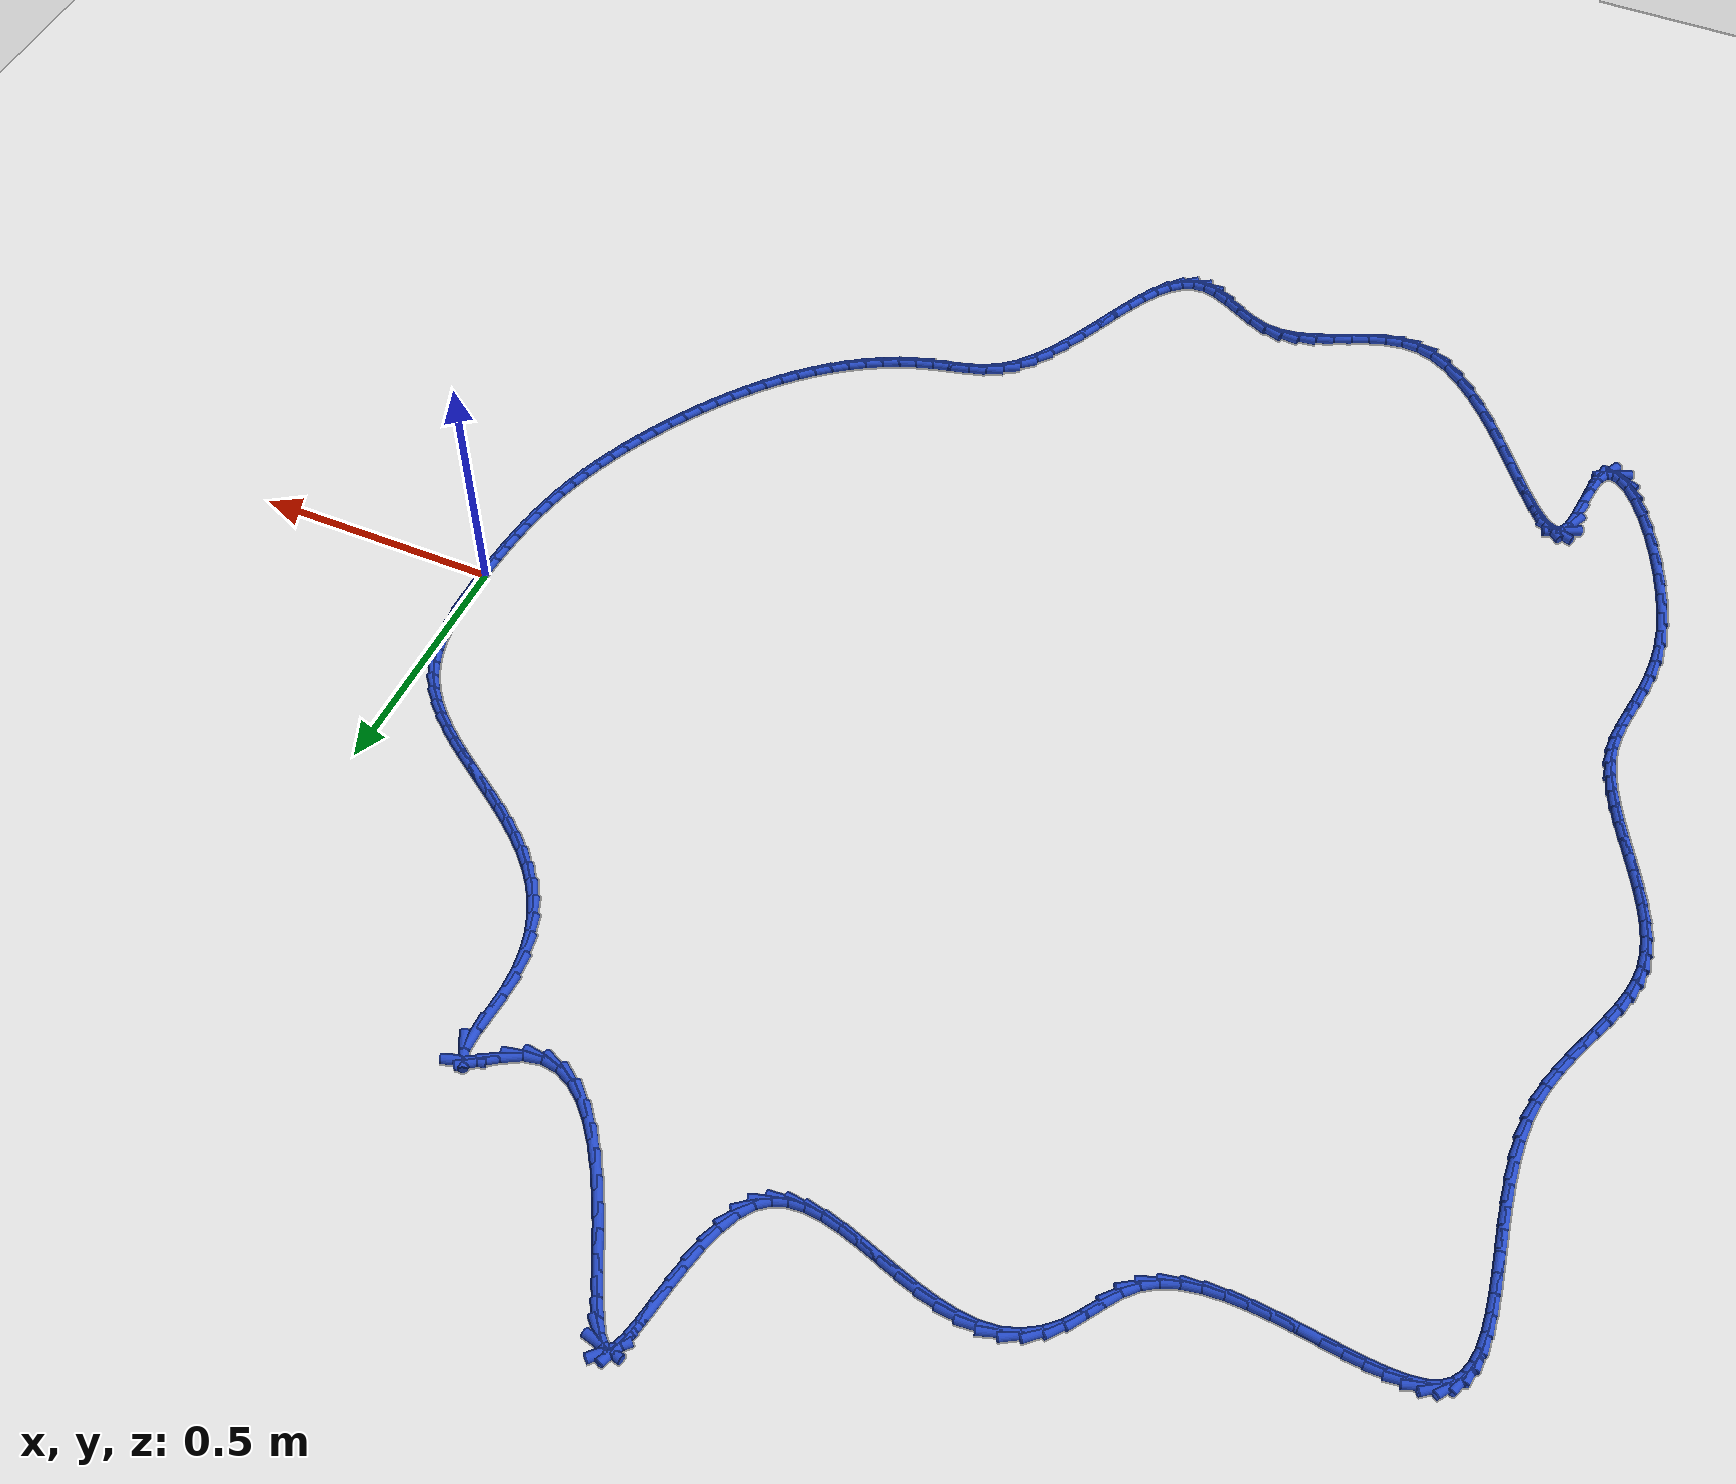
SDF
<sdf version="1.6">
 <world name="default">
  <light name="sun" type="directional">
   <pose>0 0 10 0 -0 0</pose>
   <diffuse>0.8 0.8 0.8 1</diffuse>
   <specular>0.2 0.2 0.2 1</specular>
   <attenuation>
    <range>1000</range>
    <constant>0.9</constant>
    <linear>0.01</linear>
    <quadratic>0.001</quadratic>
   </attenuation>
   <direction>-0.5 0.1 -0.9</direction>
  </light>
  <model name="ground_plane">
   <static>1</static>
   <link name="link">
    <collision name="collision">
     <geometry><plane><normal>0 0 1</normal><size>100 100</size></plane></geometry>
     <surface><friction><ode><mu>100</mu><mu2>50</mu2></ode></friction></surface>
    </collision>
    <visual name="visual">
     <cast_shadows>0</cast_shadows>
     <geometry><plane><normal>0 0 1</normal><size>100 100</size></plane></geometry>
     <material>
      <script><uri>file://media/materials/scripts/gazebo.material</uri><name>Gazebo/WhiteGlow</name></script>
     </material>
    </visual>
   </link>
  </model>
  <gravity>0 0 -9.8</gravity>
  <magnetic_field>6e-06 2.3e-05 -4.2e-05</magnetic_field>
  <atmosphere type="adiabatic"/>
  <physics name="default_physics" default="0" type="ode">
   <max_step_size>0.001</max_step_size>
   <real_time_factor>1</real_time_factor>
   <real_time_update_rate>1000</real_time_update_rate>
  </physics>
  <scene><ambient>0.4 0.4 0.4 1</ambient><background>0.7 0.7 0.7 1</background><shadows>1</shadows></scene>
  <spherical_coordinates>
   <surface_model>EARTH_WGS84</surface_model>
   <latitude_deg>0</latitude_deg>
   <longitude_deg>0</longitude_deg>
   <elevation>0</elevation>
   <heading_deg>0</heading_deg>
  </spherical_coordinates>
  <model name="line">
   <link name="link_0">
    <pose>-5.421010862427522e-18 2.0816681711721685e-17 0.01 0 1.57 1.5466712468176664</pose>
    <collision name="collision">
     <geometry><cylinder><radius>0.01</radius><length>0.08</length></cylinder></geometry>
    </collision>
    <visual name="visual">
     <material>
      <script><name>Gazebo/Blue</name><uri>file://media/materials/scripts/gazebo.material</uri></script>
     </material>
     <geometry><cylinder><radius>0.01</radius><length>0.08</length></cylinder></geometry>
    </visual>
   </link>
   <link name="link_1">
    <pose>0.0009033576102911798 0.03743748609744156 0.01 0 1.57 -1.566262863615076</pose>
    <collision name="collision">
     <geometry><cylinder><radius>0.01</radius><length>0.08</length></cylinder></geometry>
    </collision>
    <visual name="visual">
     <material>
      <script><name>Gazebo/Blue</name><uri>file://media/materials/scripts/gazebo.material</uri></script>
     </material>
     <geometry><cylinder><radius>0.01</radius><length>0.08</length></cylinder></geometry>
    </visual>
   </link>
   <link name="link_2">
    <pose>0.000733105015284847 0.07499187264290075 0.01 0 1.57 -1.5266369364941925</pose>
    <collision name="collision">
     <geometry><cylinder><radius>0.01</radius><length>0.08</length></cylinder></geometry>
    </collision>
    <visual name="visual">
     <material>
      <script><name>Gazebo/Blue</name><uri>file://media/materials/scripts/gazebo.material</uri></script>
     </material>
     <geometry><cylinder><radius>0.01</radius><length>0.08</length></cylinder></geometry>
    </visual>
   </link>
   <link name="link_3">
    <pose>-0.0009137528515199373 0.11226112003020318 0.01 0 1.57 -1.4746947276949234</pose>
    <collision name="collision">
     <geometry><cylinder><radius>0.01</radius><length>0.08</length></cylinder></geometry>
    </collision>
    <visual name="visual">
     <material>
      <script><name>Gazebo/Blue</name><uri>file://media/materials/scripts/gazebo.material</uri></script>
     </material>
     <geometry><cylinder><radius>0.01</radius><length>0.08</length></cylinder></geometry>
    </visual>
   </link>
   <link name="link_4">
    <pose>-0.004440211056624108 0.14884318865317428 0.01 0 1.57 -1.4085664133884683</pose>
    <collision name="collision">
     <geometry><cylinder><radius>0.01</radius><length>0.08</length></cylinder></geometry>
    </collision>
    <visual name="visual">
     <material>
      <script><name>Gazebo/Blue</name><uri>file://media/materials/scripts/gazebo.material</uri></script>
     </material>
     <geometry><cylinder><radius>0.01</radius><length>0.08</length></cylinder></geometry>
    </visual>
   </link>
   <link name="link_5">
    <pose>-0.01024926466652859 0.18433603890563954 0.01 0 1.57 -1.3259769424873311</pose>
    <collision name="collision">
     <geometry><cylinder><radius>0.01</radius><length>0.08</length></cylinder></geometry>
    </collision>
    <visual name="visual">
     <material>
      <script><name>Gazebo/Blue</name><uri>file://media/materials/scripts/gazebo.material</uri></script>
     </material>
     <geometry><cylinder><radius>0.01</radius><length>0.08</length></cylinder></geometry>
    </visual>
   </link>
   <link name="link_6">
    <pose>-0.018743908747734336 0.21833763118142463 0.01 0 1.57 -1.2245724802127989</pose>
    <collision name="collision">
     <geometry><cylinder><radius>0.01</radius><length>0.08</length></cylinder></geometry>
    </collision>
    <visual name="visual">
     <material>
      <script><name>Gazebo/Blue</name><uri>file://media/materials/scripts/gazebo.material</uri></script>
     </material>
     <geometry><cylinder><radius>0.01</radius><length>0.08</length></cylinder></geometry>
    </visual>
   </link>
   <link name="link_7">
    <pose>-0.030327138366742258 0.250445925874355 0.01 0 1.57 -1.1046083328242908</pose>
    <collision name="collision">
     <geometry><cylinder><radius>0.01</radius><length>0.08</length></cylinder></geometry>
    </collision>
    <visual name="visual">
     <material>
      <script><name>Gazebo/Blue</name><uri>file://media/materials/scripts/gazebo.material</uri></script>
     </material>
     <geometry><cylinder><radius>0.01</radius><length>0.08</length></cylinder></geometry>
    </visual>
   </link>
   <link name="link_8">
    <pose>-0.04535105117831094 0.28030388315494703 0.01 0 1.57 -0.9855586680049778</pose>
    <collision name="collision">
     <geometry><cylinder><radius>0.01</radius><length>0.08</length></cylinder></geometry>
    </collision>
    <visual name="visual">
     <material>
      <script><name>Gazebo/Blue</name><uri>file://media/materials/scripts/gazebo.material</uri></script>
     </material>
     <geometry><cylinder><radius>0.01</radius><length>0.08</length></cylinder></geometry>
    </visual>
   </link>
   <link name="link_9">
    <pose>-0.06368960808677686 0.30797719681140423 0.01 0 1.57 -0.8811846184135992</pose>
    <collision name="collision">
     <geometry><cylinder><radius>0.01</radius><length>0.08</length></cylinder></geometry>
    </collision>
    <visual name="visual">
     <material>
      <script><name>Gazebo/Blue</name><uri>file://media/materials/scripts/gazebo.material</uri></script>
     </material>
     <geometry><cylinder><radius>0.01</radius><length>0.08</length></cylinder></geometry>
    </visual>
   </link>
   <link name="link_10">
    <pose>-0.08495484616576891 0.3337631345664068 0.01 0 1.57 -0.793667329842581</pose>
    <collision name="collision">
     <geometry><cylinder><radius>0.01</radius><length>0.08</length></cylinder></geometry>
    </collision>
    <visual name="visual">
     <material>
      <script><name>Gazebo/Blue</name><uri>file://media/materials/scripts/gazebo.material</uri></script>
     </material>
     <geometry><cylinder><radius>0.01</radius><length>0.08</length></cylinder></geometry>
    </visual>
   </link>
   <link name="link_11">
    <pose>-0.10875612143606747 0.3579613345338865 0.01 0 1.57 -0.723325552223975</pose>
    <collision name="collision">
     <geometry><cylinder><radius>0.01</radius><length>0.08</length></cylinder></geometry>
    </collision>
    <visual name="visual">
     <material>
      <script><name>Gazebo/Blue</name><uri>file://media/materials/scripts/gazebo.material</uri></script>
     </material>
     <geometry><cylinder><radius>0.01</radius><length>0.08</length></cylinder></geometry>
    </visual>
   </link>
   <link name="link_12">
    <pose>-0.13470278991845278 0.3808714348277745 0.01 0 1.57 -0.6694469561313541</pose>
    <collision name="collision">
     <geometry><cylinder><radius>0.01</radius><length>0.08</length></cylinder></geometry>
    </collision>
    <visual name="visual">
     <material>
      <script><name>Gazebo/Blue</name><uri>file://media/materials/scripts/gazebo.material</uri></script>
     </material>
     <geometry><cylinder><radius>0.01</radius><length>0.08</length></cylinder></geometry>
    </visual>
   </link>
   <link name="link_13">
    <pose>-0.16240420763370503 0.4027930735620022 0.01 0 1.57 -0.6309139708328828</pose>
    <collision name="collision">
     <geometry><cylinder><radius>0.01</radius><length>0.08</length></cylinder></geometry>
    </collision>
    <visual name="visual">
     <material>
      <script><name>Gazebo/Blue</name><uri>file://media/materials/scripts/gazebo.material</uri></script>
     </material>
     <geometry><cylinder><radius>0.01</radius><length>0.08</length></cylinder></geometry>
    </visual>
   </link>
   <link name="link_14">
    <pose>-0.19146973060260464 0.424025888850501 0.01 0 1.57 -0.6066107967727233</pose>
    <collision name="collision">
     <geometry><cylinder><radius>0.01</radius><length>0.08</length></cylinder></geometry>
    </collision>
    <visual name="visual">
     <material>
      <script><name>Gazebo/Blue</name><uri>file://media/materials/scripts/gazebo.material</uri></script>
     </material>
     <geometry><cylinder><radius>0.01</radius><length>0.08</length></cylinder></geometry>
    </visual>
   </link>
   <link name="link_15">
    <pose>-0.2215087148459318 0.4448695188072022 0.01 0 1.57 -0.5956399887724423</pose>
    <collision name="collision">
     <geometry><cylinder><radius>0.01</radius><length>0.08</length></cylinder></geometry>
    </collision>
    <visual name="visual">
     <material>
      <script><name>Gazebo/Blue</name><uri>file://media/materials/scripts/gazebo.material</uri></script>
     </material>
     <geometry><cylinder><radius>0.01</radius><length>0.08</length></cylinder></geometry>
    </visual>
   </link>
   <link name="link_16">
    <pose>-0.25213051638446693 0.46562360154603744 0.01 0 1.57 -0.5974134192479725</pose>
    <collision name="collision">
     <geometry><cylinder><radius>0.01</radius><length>0.08</length></cylinder></geometry>
    </collision>
    <visual name="visual">
     <material>
      <script><name>Gazebo/Blue</name><uri>file://media/materials/scripts/gazebo.material</uri></script>
     </material>
     <geometry><cylinder><radius>0.01</radius><length>0.08</length></cylinder></geometry>
    </visual>
   </link>
   <link name="link_17">
    <pose>-0.2829444912389901 0.4865877751809377 0.01 0 1.57 -0.6116690597869092</pose>
    <collision name="collision">
     <geometry><cylinder><radius>0.01</radius><length>0.08</length></cylinder></geometry>
    </collision>
    <visual name="visual">
     <material>
      <script><name>Gazebo/Blue</name><uri>file://media/materials/scripts/gazebo.material</uri></script>
     </material>
     <geometry><cylinder><radius>0.01</radius><length>0.08</length></cylinder></geometry>
    </visual>
   </link>
   <link name="link_18">
    <pose>-0.31355999543028185 0.5080616778258348 0.01 0 1.57 -0.6384406416458243</pose>
    <collision name="collision">
     <geometry><cylinder><radius>0.01</radius><length>0.08</length></cylinder></geometry>
    </collision>
    <visual name="visual">
     <material>
      <script><name>Gazebo/Blue</name><uri>file://media/materials/scripts/gazebo.material</uri></script>
     </material>
     <geometry><cylinder><radius>0.01</radius><length>0.08</length></cylinder></geometry>
    </visual>
   </link>
   <link name="link_19">
    <pose>-0.34358638497912225 0.5303449475946596 0.01 0 1.57 -0.6779856712423643</pose>
    <collision name="collision">
     <geometry><cylinder><radius>0.01</radius><length>0.08</length></cylinder></geometry>
    </collision>
    <visual name="visual">
     <material>
      <script><name>Gazebo/Blue</name><uri>file://media/materials/scripts/gazebo.material</uri></script>
     </material>
     <geometry><cylinder><radius>0.01</radius><length>0.08</length></cylinder></geometry>
    </visual>
   </link>
   <link name="link_20">
    <pose>-0.37263301590629183 0.553737222601344 0.01 0 1.57 -0.730661235544265</pose>
    <collision name="collision">
     <geometry><cylinder><radius>0.01</radius><length>0.08</length></cylinder></geometry>
    </collision>
    <visual name="visual">
     <material>
      <script><name>Gazebo/Blue</name><uri>file://media/materials/scripts/gazebo.material</uri></script>
     </material>
     <geometry><cylinder><radius>0.01</radius><length>0.08</length></cylinder></geometry>
    </visual>
   </link>
   <link name="link_21">
    <pose>-0.40030924423257064 0.578538140959819 0.01 0 1.57 -0.7967286291104057</pose>
    <collision name="collision">
     <geometry><cylinder><radius>0.01</radius><length>0.08</length></cylinder></geometry>
    </collision>
    <visual name="visual">
     <material>
      <script><name>Gazebo/Blue</name><uri>file://media/materials/scripts/gazebo.material</uri></script>
     </material>
     <geometry><cylinder><radius>0.01</radius><length>0.08</length></cylinder></geometry>
    </visual>
   </link>
   <link name="link_22">
    <pose>-0.426224425978739 0.6050473407840163 0.01 0 1.57 -0.8760740891448919</pose>
    <collision name="collision">
     <geometry><cylinder><radius>0.01</radius><length>0.08</length></cylinder></geometry>
    </collision>
    <visual name="visual">
     <material>
      <script><name>Gazebo/Blue</name><uri>file://media/materials/scripts/gazebo.material</uri></script>
     </material>
     <geometry><cylinder><radius>0.01</radius><length>0.08</length></cylinder></geometry>
    </visual>
   </link>
   <link name="link_23">
    <pose>-0.44998791716557723 0.6335644601878669 0.01 0 1.57 -0.9678662053726462</pose>
    <collision name="collision">
     <geometry><cylinder><radius>0.01</radius><length>0.08</length></cylinder></geometry>
    </collision>
    <visual name="visual">
     <material>
      <script><name>Gazebo/Blue</name><uri>file://media/materials/scripts/gazebo.material</uri></script>
     </material>
     <geometry><cylinder><radius>0.01</radius><length>0.08</length></cylinder></geometry>
    </visual>
   </link>
   <link name="link_24">
    <pose>-0.4712090738138658 0.6643891372853026 0.01 0 1.57 -1.0702375708480145</pose>
    <collision name="collision">
     <geometry><cylinder><radius>0.01</radius><length>0.08</length></cylinder></geometry>
    </collision>
    <visual name="visual">
     <material>
      <script><name>Gazebo/Blue</name><uri>file://media/materials/scripts/gazebo.material</uri></script>
     </material>
     <geometry><cylinder><radius>0.01</radius><length>0.08</length></cylinder></geometry>
    </visual>
   </link>
   <link name="link_25">
    <pose>-0.48949725194438476 0.6978210101902544 0.01 0 1.57 -1.1801526081879898</pose>
    <collision name="collision">
     <geometry><cylinder><radius>0.01</radius><length>0.08</length></cylinder></geometry>
    </collision>
    <visual name="visual">
     <material>
      <script><name>Gazebo/Blue</name><uri>file://media/materials/scripts/gazebo.material</uri></script>
     </material>
     <geometry><cylinder><radius>0.01</radius><length>0.08</length></cylinder></geometry>
    </visual>
   </link>
   <link name="link_26">
    <pose>-0.5044618075779144 0.7341597170166541 0.01 0 1.57 -1.2936270201252125</pose>
    <collision name="collision">
     <geometry><cylinder><radius>0.01</radius><length>0.08</length></cylinder></geometry>
    </collision>
    <visual name="visual">
     <material>
      <script><name>Gazebo/Blue</name><uri>file://media/materials/scripts/gazebo.material</uri></script>
     </material>
     <geometry><cylinder><radius>0.01</radius><length>0.08</length></cylinder></geometry>
    </visual>
   </link>
   <link name="link_27">
    <pose>-0.5157120967352352 0.7737048958784327 0.01 0 1.57 -1.40632203127292</pose>
    <collision name="collision">
     <geometry><cylinder><radius>0.01</radius><length>0.08</length></cylinder></geometry>
    </collision>
    <visual name="visual">
     <material>
      <script><name>Gazebo/Blue</name><uri>file://media/materials/scripts/gazebo.material</uri></script>
     </material>
     <geometry><cylinder><radius>0.01</radius><length>0.08</length></cylinder></geometry>
    </visual>
   </link>
   <link name="link_28">
    <pose>-0.5228574754371271 0.8167561848895213 0.01 0 1.57 -1.5143052407777957</pose>
    <collision name="collision">
     <geometry><cylinder><radius>0.01</radius><length>0.08</length></cylinder></geometry>
    </collision>
    <visual name="visual">
     <material>
      <script><name>Gazebo/Blue</name><uri>file://media/materials/scripts/gazebo.material</uri></script>
     </material>
     <geometry><cylinder><radius>0.01</radius><length>0.08</length></cylinder></geometry>
    </visual>
   </link>
   <link name="link_29">
    <pose>-0.5255072997043708 0.8636132221638523 0.01 0 1.57 1.5336267240267973</pose>
    <collision name="collision">
     <geometry><cylinder><radius>0.01</radius><length>0.08</length></cylinder></geometry>
    </collision>
    <visual name="visual">
     <material>
      <script><name>Gazebo/Blue</name><uri>file://media/materials/scripts/gazebo.material</uri></script>
     </material>
     <geometry><cylinder><radius>0.01</radius><length>0.08</length></cylinder></geometry>
    </visual>
   </link>
   <link name="link_30">
    <pose>-0.5236342044104434 0.9139832144451312 0.01 0 1.57 1.5058906544428745</pose>
    <collision name="collision">
     <geometry><cylinder><radius>0.01</radius><length>0.08</length></cylinder></geometry>
    </collision>
    <visual name="visual">
     <material>
      <script><name>Gazebo/Blue</name><uri>file://media/materials/scripts/gazebo.material</uri></script>
     </material>
     <geometry><cylinder><radius>0.01</radius><length>0.08</length></cylinder></geometry>
    </visual>
   </link>
   <link name="link_31">
    <pose>-0.5204996056959212 0.9622100582321327 0.01 0 1.57 -1.5544566644169127</pose>
    <collision name="collision">
     <geometry><cylinder><radius>0.01</radius><length>0.08</length></cylinder></geometry>
    </collision>
    <visual name="visual">
     <material>
      <script><name>Gazebo/Blue</name><uri>file://media/materials/scripts/gazebo.material</uri></script>
     </material>
     <geometry><cylinder><radius>0.01</radius><length>0.08</length></cylinder></geometry>
    </visual>
   </link>
   <link name="link_32">
    <pose>-0.5211136362772006 0.9997858612408371 0.01 0 1.57 -1.098756208059924</pose>
    <collision name="collision">
     <geometry><cylinder><radius>0.01</radius><length>0.08</length></cylinder></geometry>
    </collision>
    <visual name="visual">
     <material>
      <script><name>Gazebo/Blue</name><uri>file://media/materials/scripts/gazebo.material</uri></script>
     </material>
     <geometry><cylinder><radius>0.01</radius><length>0.08</length></cylinder></geometry>
    </visual>
   </link>
   <link name="link_33">
    <pose>-0.5305026169132392 1.0181763318959782 0.01 0 1.57 0.316375865510194</pose>
    <collision name="collision">
     <geometry><cylinder><radius>0.01</radius><length>0.08</length></cylinder></geometry>
    </collision>
    <visual name="visual">
     <material>
      <script><name>Gazebo/Blue</name><uri>file://media/materials/scripts/gazebo.material</uri></script>
     </material>
     <geometry><cylinder><radius>0.01</radius><length>0.08</length></cylinder></geometry>
    </visual>
   </link>
   <link name="link_34">
    <pose>-0.5528246898223239 1.0108687084722598 0.01 0 1.57 0.6171004172588965</pose>
    <collision name="collision">
     <geometry><cylinder><radius>0.01</radius><length>0.08</length></cylinder></geometry>
    </collision>
    <visual name="visual">
     <material>
      <script><name>Gazebo/Blue</name><uri>file://media/materials/scripts/gazebo.material</uri></script>
     </material>
     <geometry><cylinder><radius>0.01</radius><length>0.08</length></cylinder></geometry>
    </visual>
   </link>
   <link name="link_35">
    <pose>-0.585101726474419 0.9879668393762887 0.01 0 1.57 0.5172918394940162</pose>
    <collision name="collision">
     <geometry><cylinder><radius>0.01</radius><length>0.08</length></cylinder></geometry>
    </collision>
    <visual name="visual">
     <material>
      <script><name>Gazebo/Blue</name><uri>file://media/materials/scripts/gazebo.material</uri></script>
     </material>
     <geometry><cylinder><radius>0.01</radius><length>0.08</length></cylinder></geometry>
    </visual>
   </link>
   <link name="link_36">
    <pose>-0.6208938036519871 0.9676021704015383 0.01 0 1.57 0.19968713856347467</pose>
    <collision name="collision">
     <geometry><cylinder><radius>0.01</radius><length>0.08</length></cylinder></geometry>
    </collision>
    <visual name="visual">
     <material>
      <script><name>Gazebo/Blue</name><uri>file://media/materials/scripts/gazebo.material</uri></script>
     </material>
     <geometry><cylinder><radius>0.01</radius><length>0.08</length></cylinder></geometry>
    </visual>
   </link>
   <link name="link_37">
    <pose>-0.6561391204100299 0.9604690702731081 0.01 0 1.57 -0.15527746993978175</pose>
    <collision name="collision">
     <geometry><cylinder><radius>0.01</radius><length>0.08</length></cylinder></geometry>
    </collision>
    <visual name="visual">
     <material>
      <script><name>Gazebo/Blue</name><uri>file://media/materials/scripts/gazebo.material</uri></script>
     </material>
     <geometry><cylinder><radius>0.01</radius><length>0.08</length></cylinder></geometry>
    </visual>
   </link>
   <link name="link_38">
    <pose>-0.6904382300921198 0.9658381703910786 0.01 0 1.57 -0.4527787735282066</pose>
    <collision name="collision">
     <geometry><cylinder><radius>0.01</radius><length>0.08</length></cylinder></geometry>
    </collision>
    <visual name="visual">
     <material>
      <script><name>Gazebo/Blue</name><uri>file://media/materials/scripts/gazebo.material</uri></script>
     </material>
     <geometry><cylinder><radius>0.01</radius><length>0.08</length></cylinder></geometry>
    </visual>
   </link>
   <link name="link_39">
    <pose>-0.7236996712509711 0.9820194244460648 0.01 0 1.57 -0.6670563724619244</pose>
    <collision name="collision">
     <geometry><cylinder><radius>0.01</radius><length>0.08</length></cylinder></geometry>
    </collision>
    <visual name="visual">
     <material>
      <script><name>Gazebo/Blue</name><uri>file://media/materials/scripts/gazebo.material</uri></script>
     </material>
     <geometry><cylinder><radius>0.01</radius><length>0.08</length></cylinder></geometry>
    </visual>
   </link>
   <link name="link_40">
    <pose>-0.7558319824392966 1.0073227861286804 0.01 0 1.57 -0.8140436657945415</pose>
    <collision name="collision">
     <geometry><cylinder><radius>0.01</radius><length>0.08</length></cylinder></geometry>
    </collision>
    <visual name="visual">
     <material>
      <script><name>Gazebo/Blue</name><uri>file://media/materials/scripts/gazebo.material</uri></script>
     </material>
     <geometry><cylinder><radius>0.01</radius><length>0.08</length></cylinder></geometry>
    </visual>
   </link>
   <link name="link_41">
    <pose>-0.7867437022098097 1.040058209129539 0.01 0 1.57 -0.915073961564052</pose>
    <collision name="collision">
     <geometry><cylinder><radius>0.01</radius><length>0.08</length></cylinder></geometry>
    </collision>
    <visual name="visual">
     <material>
      <script><name>Gazebo/Blue</name><uri>file://media/materials/scripts/gazebo.material</uri></script>
     </material>
     <geometry><cylinder><radius>0.01</radius><length>0.08</length></cylinder></geometry>
    </visual>
   </link>
   <link name="link_42">
    <pose>-0.8163433691152232 1.0785356471392544 0.01 0 1.57 -0.9853502689129733</pose>
    <collision name="collision">
     <geometry><cylinder><radius>0.01</radius><length>0.08</length></cylinder></geometry>
    </collision>
    <visual name="visual">
     <material>
      <script><name>Gazebo/Blue</name><uri>file://media/materials/scripts/gazebo.material</uri></script>
     </material>
     <geometry><cylinder><radius>0.01</radius><length>0.08</length></cylinder></geometry>
    </visual>
   </link>
   <link name="link_43">
    <pose>-0.8445395217082511 1.1210650538484415 0.01 0 1.57 -1.0342121848393835</pose>
    <collision name="collision">
     <geometry><cylinder><radius>0.01</radius><length>0.08</length></cylinder></geometry>
    </collision>
    <visual name="visual">
     <material>
      <script><name>Gazebo/Blue</name><uri>file://media/materials/scripts/gazebo.material</uri></script>
     </material>
     <geometry><cylinder><radius>0.01</radius><length>0.08</length></cylinder></geometry>
    </visual>
   </link>
   <link name="link_44">
    <pose>-0.8712406985416061 1.1659563829477138 0.01 0 1.57 -1.0670272119185962</pose>
    <collision name="collision">
     <geometry><cylinder><radius>0.01</radius><length>0.08</length></cylinder></geometry>
    </collision>
    <visual name="visual">
     <material>
      <script><name>Gazebo/Blue</name><uri>file://media/materials/scripts/gazebo.material</uri></script>
     </material>
     <geometry><cylinder><radius>0.01</radius><length>0.08</length></cylinder></geometry>
    </visual>
   </link>
   <link name="link_45">
    <pose>-0.8963554381680019 1.2115195881276852 0.01 0 1.57 -1.0864575369189962</pose>
    <collision name="collision">
     <geometry><cylinder><radius>0.01</radius><length>0.08</length></cylinder></geometry>
    </collision>
    <visual name="visual">
     <material>
      <script><name>Gazebo/Blue</name><uri>file://media/materials/scripts/gazebo.material</uri></script>
     </material>
     <geometry><cylinder><radius>0.01</radius><length>0.08</length></cylinder></geometry>
    </visual>
   </link>
   <link name="link_46">
    <pose>-0.9197922791401514 1.2560646230789696 0.01 0 1.57 -1.0929278478432178</pose>
    <collision name="collision">
     <geometry><cylinder><radius>0.01</radius><length>0.08</length></cylinder></geometry>
    </collision>
    <visual name="visual">
     <material>
      <script><name>Gazebo/Blue</name><uri>file://media/materials/scripts/gazebo.material</uri></script>
     </material>
     <geometry><cylinder><radius>0.01</radius><length>0.08</length></cylinder></geometry>
    </visual>
   </link>
   <link name="link_47">
    <pose>-0.9414597600107681 1.2979014414921815 0.01 0 1.57 -1.0841840560757736</pose>
    <collision name="collision">
     <geometry><cylinder><radius>0.01</radius><length>0.08</length></cylinder></geometry>
    </collision>
    <visual name="visual">
     <material>
      <script><name>Gazebo/Blue</name><uri>file://media/materials/scripts/gazebo.material</uri></script>
     </material>
     <geometry><cylinder><radius>0.01</radius><length>0.08</length></cylinder></geometry>
    </visual>
   </link>
   <link name="link_48">
    <pose>-0.9612664193325654 1.3353399970579345 0.01 0 1.57 -1.0530953673450079</pose>
    <collision name="collision">
     <geometry><cylinder><radius>0.01</radius><length>0.08</length></cylinder></geometry>
    </collision>
    <visual name="visual">
     <material>
      <script><name>Gazebo/Blue</name><uri>file://media/materials/scripts/gazebo.material</uri></script>
     </material>
     <geometry><cylinder><radius>0.01</radius><length>0.08</length></cylinder></geometry>
    </visual>
   </link>
   <link name="link_49">
    <pose>-0.979120795658256 1.3666902434668424 0.01 0 1.57 -0.9799783858928658</pose>
    <collision name="collision">
     <geometry><cylinder><radius>0.01</radius><length>0.08</length></cylinder></geometry>
    </collision>
    <visual name="visual">
     <material>
      <script><name>Gazebo/Blue</name><uri>file://media/materials/scripts/gazebo.material</uri></script>
     </material>
     <geometry><cylinder><radius>0.01</radius><length>0.08</length></cylinder></geometry>
    </visual>
   </link>
   <link name="link_50">
    <pose>-0.9949314275405539 1.3902621344095194 0.01 0 1.57 -0.8008065872185016</pose>
    <collision name="collision">
     <geometry><cylinder><radius>0.01</radius><length>0.08</length></cylinder></geometry>
    </collision>
    <visual name="visual">
     <material>
      <script><name>Gazebo/Blue</name><uri>file://media/materials/scripts/gazebo.material</uri></script>
     </material>
     <geometry><cylinder><radius>0.01</radius><length>0.08</length></cylinder></geometry>
    </visual>
   </link>
   <link name="link_51">
    <pose>-1.0086068535321717 1.4043656235765793 0.01 0 1.57 -0.25177800766509945</pose>
    <collision name="collision">
     <geometry><cylinder><radius>0.01</radius><length>0.08</length></cylinder></geometry>
    </collision>
    <visual name="visual">
     <material>
      <script><name>Gazebo/Blue</name><uri>file://media/materials/scripts/gazebo.material</uri></script>
     </material>
     <geometry><cylinder><radius>0.01</radius><length>0.08</length></cylinder></geometry>
    </visual>
   </link>
   <link name="link_52">
    <pose>-1.0200556121858233 1.4073106646586369 0.01 0 1.57 0.8142496472517692</pose>
    <collision name="collision">
     <geometry><cylinder><radius>0.01</radius><length>0.08</length></cylinder></geometry>
    </collision>
    <visual name="visual">
     <material>
      <script><name>Gazebo/Blue</name><uri>file://media/materials/scripts/gazebo.material</uri></script>
     </material>
     <geometry><cylinder><radius>0.01</radius><length>0.08</length></cylinder></geometry>
    </visual>
   </link>
   <link name="link_53">
    <pose>-1.0292241540810445 1.3975971975778665 0.01 0 1.57 1.243759623597403</pose>
    <collision name="collision">
     <geometry><cylinder><radius>0.01</radius><length>0.08</length></cylinder></geometry>
    </collision>
    <visual name="visual">
     <material>
      <script><name>Gazebo/Blue</name><uri>file://media/materials/scripts/gazebo.material</uri></script>
     </material>
     <geometry><cylinder><radius>0.01</radius><length>0.08</length></cylinder></geometry>
    </visual>
   </link>
   <link name="link_54">
    <pose>-1.0365267364347919 1.3760694531738997 0.01 0 1.57 1.3739480152820807</pose>
    <collision name="collision">
     <geometry><cylinder><radius>0.01</radius><length>0.08</length></cylinder></geometry>
    </collision>
    <visual name="visual">
     <material>
      <script><name>Gazebo/Blue</name><uri>file://media/materials/scripts/gazebo.material</uri></script>
     </material>
     <geometry><cylinder><radius>0.01</radius><length>0.08</length></cylinder></geometry>
    </visual>
   </link>
   <link name="link_55">
    <pose>-1.0426928038604086 1.3451511416941782 0.01 0 1.57 1.419671485891712</pose>
    <collision name="collision">
     <geometry><cylinder><radius>0.01</radius><length>0.08</length></cylinder></geometry>
    </collision>
    <visual name="visual">
     <material>
      <script><name>Gazebo/Blue</name><uri>file://media/materials/scripts/gazebo.material</uri></script>
     </material>
     <geometry><cylinder><radius>0.01</radius><length>0.08</length></cylinder></geometry>
    </visual>
   </link>
   <link name="link_56">
    <pose>-1.048457689143691 1.3072954804262291 0.01 0 1.57 1.4277307308949199</pose>
    <collision name="collision">
     <geometry><cylinder><radius>0.01</radius><length>0.08</length></cylinder></geometry>
    </collision>
    <visual name="visual">
     <material>
      <script><name>Gazebo/Blue</name><uri>file://media/materials/scripts/gazebo.material</uri></script>
     </material>
     <geometry><cylinder><radius>0.01</radius><length>0.08</length></cylinder></geometry>
    </visual>
   </link>
   <link name="link_57">
    <pose>-1.054556725070434 1.2649556866575782 0.01 0 1.57 1.4106206470998635</pose>
    <collision name="collision">
     <geometry><cylinder><radius>0.01</radius><length>0.08</length></cylinder></geometry>
    </collision>
    <visual name="visual">
     <material>
      <script><name>Gazebo/Blue</name><uri>file://media/materials/scripts/gazebo.material</uri></script>
     </material>
     <geometry><cylinder><radius>0.01</radius><length>0.08</length></cylinder></geometry>
    </visual>
   </link>
   <link name="link_58">
    <pose>-1.061725244426434 1.2205849776757518 0.01 0 1.57 1.3693858814854973</pose>
    <collision name="collision">
     <geometry><cylinder><radius>0.01</radius><length>0.08</length></cylinder></geometry>
    </collision>
    <visual name="visual">
     <material>
      <script><name>Gazebo/Blue</name><uri>file://media/materials/scripts/gazebo.material</uri></script>
     </material>
     <geometry><cylinder><radius>0.01</radius><length>0.08</length></cylinder></geometry>
    </visual>
   </link>
   <link name="link_59">
    <pose>-1.0706985799974862 1.1766365707682762 0.01 0 1.57 1.2974924308471159</pose>
    <collision name="collision">
     <geometry><cylinder><radius>0.01</radius><length>0.08</length></cylinder></geometry>
    </collision>
    <visual name="visual">
     <material>
      <script><name>Gazebo/Blue</name><uri>file://media/materials/scripts/gazebo.material</uri></script>
     </material>
     <geometry><cylinder><radius>0.01</radius><length>0.08</length></cylinder></geometry>
    </visual>
   </link>
   <link name="link_60">
    <pose>-1.0822120645693871 1.1355636832226774 0.01 0 1.57 1.1784971911372524</pose>
    <collision name="collision">
     <geometry><cylinder><radius>0.01</radius><length>0.08</length></cylinder></geometry>
    </collision>
    <visual name="visual">
     <material>
      <script><name>Gazebo/Blue</name><uri>file://media/materials/scripts/gazebo.material</uri></script>
     </material>
     <geometry><cylinder><radius>0.01</radius><length>0.08</length></cylinder></geometry>
    </visual>
   </link>
   <link name="link_61">
    <pose>-1.0970010309279314 1.099819532326482 0.01 0 1.57 0.9788855205143832</pose>
    <collision name="collision">
     <geometry><cylinder><radius>0.01</radius><length>0.08</length></cylinder></geometry>
    </collision>
    <visual name="visual">
     <material>
      <script><name>Gazebo/Blue</name><uri>file://media/materials/scripts/gazebo.material</uri></script>
     </material>
     <geometry><cylinder><radius>0.01</radius><length>0.08</length></cylinder></geometry>
    </visual>
   </link>
   <link name="link_62">
    <pose>-1.1158007946173771 1.0718572844889462 0.01 0 1.57 0.6696522102916078</pose>
    <collision name="collision">
     <geometry><cylinder><radius>0.01</radius><length>0.08</length></cylinder></geometry>
    </collision>
    <visual name="visual">
     <material>
      <script><name>Gazebo/Blue</name><uri>file://media/materials/scripts/gazebo.material</uri></script>
     </material>
     <geometry><cylinder><radius>0.01</radius><length>0.08</length></cylinder></geometry>
    </visual>
   </link>
   <link name="link_63">
    <pose>-1.139102505309041 1.0534095940477959 0.01 0 1.57 0.3409156343845132</pose>
    <collision name="collision">
     <geometry><cylinder><radius>0.01</radius><length>0.08</length></cylinder></geometry>
    </collision>
    <visual name="visual">
     <material>
      <script><name>Gazebo/Blue</name><uri>file://media/materials/scripts/gazebo.material</uri></script>
     </material>
     <geometry><cylinder><radius>0.01</radius><length>0.08</length></cylinder></geometry>
    </visual>
   </link>
   <link name="link_64">
    <pose>-1.1665389121778005 1.0436760507791685 0.01 0 1.57 0.07646337659949173</pose>
    <collision name="collision">
     <geometry><cylinder><radius>0.01</radius><length>0.08</length></cylinder></geometry>
    </collision>
    <visual name="visual">
     <material>
      <script><name>Gazebo/Blue</name><uri>file://media/materials/scripts/gazebo.material</uri></script>
     </material>
     <geometry><cylinder><radius>0.01</radius><length>0.08</length></cylinder></geometry>
    </visual>
   </link>
   <link name="link_65">
    <pose>-1.1975542254365463 1.041299882522004 0.01 0 1.57 -0.10608094852840963</pose>
    <collision name="collision">
     <geometry><cylinder><radius>0.01</radius><length>0.08</length></cylinder></geometry>
    </collision>
    <visual name="visual">
     <material>
      <script><name>Gazebo/Blue</name><uri>file://media/materials/scripts/gazebo.material</uri></script>
     </material>
     <geometry><cylinder><radius>0.01</radius><length>0.08</length></cylinder></geometry>
    </visual>
   </link>
   <link name="link_66">
    <pose>-1.2315926552981704 1.0449243171152431 0.01 0 1.57 -0.2227341845248011</pose>
    <collision name="collision">
     <geometry><cylinder><radius>0.01</radius><length>0.08</length></cylinder></geometry>
    </collision>
    <visual name="visual">
     <material>
      <script><name>Gazebo/Blue</name><uri>file://media/materials/scripts/gazebo.material</uri></script>
     </material>
     <geometry><cylinder><radius>0.01</radius><length>0.08</length></cylinder></geometry>
    </visual>
   </link>
   <link name="link_67">
    <pose>-1.2680984119755623 1.053192582397827 0.01 0 1.57 -0.2921763000739865</pose>
    <collision name="collision">
     <geometry><cylinder><radius>0.01</radius><length>0.08</length></cylinder></geometry>
    </collision>
    <visual name="visual">
     <material>
      <script><name>Gazebo/Blue</name><uri>file://media/materials/scripts/gazebo.material</uri></script>
     </material>
     <geometry><cylinder><radius>0.01</radius><length>0.08</length></cylinder></geometry>
    </visual>
   </link>
   <link name="link_68">
    <pose>-1.3065157056816135 1.064747906208696 0.01 0 1.57 -0.32689934336442095</pose>
    <collision name="collision">
     <geometry><cylinder><radius>0.01</radius><length>0.08</length></cylinder></geometry>
    </collision>
    <visual name="visual">
     <material>
      <script><name>Gazebo/Blue</name><uri>file://media/materials/scripts/gazebo.material</uri></script>
     </material>
     <geometry><cylinder><radius>0.01</radius><length>0.08</length></cylinder></geometry>
    </visual>
   </link>
   <link name="link_69">
    <pose>-1.3462887466292144 1.078233516386791 0.01 0 1.57 -0.33356615541894824</pose>
    <collision name="collision">
     <geometry><cylinder><radius>0.01</radius><length>0.08</length></cylinder></geometry>
    </collision>
    <visual name="visual">
     <material>
      <script><name>Gazebo/Blue</name><uri>file://media/materials/scripts/gazebo.material</uri></script>
     </material>
     <geometry><cylinder><radius>0.01</radius><length>0.08</length></cylinder></geometry>
    </visual>
   </link>
   <link name="link_70">
    <pose>-1.3868617450312566 1.0922926407710538 0.01 0 1.57 -0.314459841499243</pose>
    <collision name="collision">
     <geometry><cylinder><radius>0.01</radius><length>0.08</length></cylinder></geometry>
    </collision>
    <visual name="visual">
     <material>
      <script><name>Gazebo/Blue</name><uri>file://media/materials/scripts/gazebo.material</uri></script>
     </material>
     <geometry><cylinder><radius>0.01</radius><length>0.08</length></cylinder></geometry>
    </visual>
   </link>
   <link name="link_71">
    <pose>-1.4276789111006298 1.1055685072004242 0.01 0 1.57 -0.2682930315056576</pose>
    <collision name="collision">
     <geometry><cylinder><radius>0.01</radius><length>0.08</length></cylinder></geometry>
    </collision>
    <visual name="visual">
     <material>
      <script><name>Gazebo/Blue</name><uri>file://media/materials/scripts/gazebo.material</uri></script>
     </material>
     <geometry><cylinder><radius>0.01</radius><length>0.08</length></cylinder></geometry>
    </visual>
   </link>
   <link name="link_72">
    <pose>-1.4681844550502254 1.116704343513843 0.01 0 1.57 -0.19038520972658035</pose>
    <collision name="collision">
     <geometry><cylinder><radius>0.01</radius><length>0.08</length></cylinder></geometry>
    </collision>
    <visual name="visual">
     <material>
      <script><name>Gazebo/Blue</name><uri>file://media/materials/scripts/gazebo.material</uri></script>
     </material>
     <geometry><cylinder><radius>0.01</radius><length>0.08</length></cylinder></geometry>
    </visual>
   </link>
   <link name="link_73">
    <pose>-1.507822587092934 1.1243433775502516 0.01 0 1.57 -0.07276062858761857</pose>
    <collision name="collision">
     <geometry><cylinder><radius>0.01</radius><length>0.08</length></cylinder></geometry>
    </collision>
    <visual name="visual">
     <material>
      <script><name>Gazebo/Blue</name><uri>file://media/materials/scripts/gazebo.material</uri></script>
     </material>
     <geometry><cylinder><radius>0.01</radius><length>0.08</length></cylinder></geometry>
    </visual>
   </link>
   <link name="link_74">
    <pose>-1.5460375174416474 1.1271288371485908 0.01 0 1.57 0.09423635415098695</pose>
    <collision name="collision">
     <geometry><cylinder><radius>0.01</radius><length>0.08</length></cylinder></geometry>
    </collision>
    <visual name="visual">
     <material>
      <script><name>Gazebo/Blue</name><uri>file://media/materials/scripts/gazebo.material</uri></script>
     </material>
     <geometry><cylinder><radius>0.01</radius><length>0.08</length></cylinder></geometry>
    </visual>
   </link>
   <link name="link_75">
    <pose>-1.5822734563092546 1.1237039501478006 0.01 0 1.57 0.31483431000690837</pose>
    <collision name="collision">
     <geometry><cylinder><radius>0.01</radius><length>0.08</length></cylinder></geometry>
    </collision>
    <visual name="visual">
     <material>
      <script><name>Gazebo/Blue</name><uri>file://media/materials/scripts/gazebo.material</uri></script>
     </material>
     <geometry><cylinder><radius>0.01</radius><length>0.08</length></cylinder></geometry>
    </visual>
   </link>
   <link name="link_76">
    <pose>-1.6159742591710073 1.1127287387174178 0.01 0 1.57 0.5498756850519348</pose>
    <collision name="collision">
     <geometry><cylinder><radius>0.01</radius><length>0.08</length></cylinder></geometry>
    </collision>
    <visual name="visual">
     <material>
      <script><name>Gazebo/Blue</name><uri>file://media/materials/scripts/gazebo.material</uri></script>
     </material>
     <geometry><cylinder><radius>0.01</radius><length>0.08</length></cylinder></geometry>
    </visual>
   </link>
   <link name="link_77">
    <pose>-1.646560158764855 1.0939815953803158 0.01 0 1.57 0.7484829596003867</pose>
    <collision name="collision">
     <geometry><cylinder><radius>0.01</radius><length>0.08</length></cylinder></geometry>
    </collision>
    <visual name="visual">
     <material>
      <script><name>Gazebo/Blue</name><uri>file://media/materials/scripts/gazebo.material</uri></script>
     </material>
     <geometry><cylinder><radius>0.01</radius><length>0.08</length></cylinder></geometry>
    </visual>
   </link>
   <link name="link_78">
    <pose>-1.6734133606384975 1.0690412324804133 0.01 0 1.57 0.9147731280634256</pose>
    <collision name="collision">
     <geometry><cylinder><radius>0.01</radius><length>0.08</length></cylinder></geometry>
    </collision>
    <visual name="visual">
     <material>
      <script><name>Gazebo/Blue</name><uri>file://media/materials/scripts/gazebo.material</uri></script>
     </material>
     <geometry><cylinder><radius>0.01</radius><length>0.08</length></cylinder></geometry>
    </visual>
   </link>
   <link name="link_79">
    <pose>-1.696006985462086 1.0396894205603493 0.01 0 1.57 1.0081198870486294</pose>
    <collision name="collision">
     <geometry><cylinder><radius>0.01</radius><length>0.08</length></cylinder></geometry>
    </collision>
    <visual name="visual">
     <material>
      <script><name>Gazebo/Blue</name><uri>file://media/materials/scripts/gazebo.material</uri></script>
     </material>
     <geometry><cylinder><radius>0.01</radius><length>0.08</length></cylinder></geometry>
    </visual>
   </link>
   <link name="link_80">
    <pose>-1.7156776514218863 1.0085000172722427 0.01 0 1.57 0.983408410773953</pose>
    <collision name="collision">
     <geometry><cylinder><radius>0.01</radius><length>0.08</length></cylinder></geometry>
    </collision>
    <visual name="visual">
     <material>
      <script><name>Gazebo/Blue</name><uri>file://media/materials/scripts/gazebo.material</uri></script>
     </material>
     <geometry><cylinder><radius>0.01</radius><length>0.08</length></cylinder></geometry>
    </visual>
   </link>
   <link name="link_81">
    <pose>-1.7354694995557867 0.9787726697196207 0.01 0 1.57 0.8259656421179257</pose>
    <collision name="collision">
     <geometry><cylinder><radius>0.01</radius><length>0.08</length></cylinder></geometry>
    </collision>
    <visual name="visual">
     <material>
      <script><name>Gazebo/Blue</name><uri>file://media/materials/scripts/gazebo.material</uri></script>
     </material>
     <geometry><cylinder><radius>0.01</radius><length>0.08</length></cylinder></geometry>
    </visual>
   </link>
   <link name="link_82">
    <pose>-1.7584762272893177 0.9538192517772164 0.01 0 1.57 0.5776786630187335</pose>
    <collision name="collision">
     <geometry><cylinder><radius>0.01</radius><length>0.08</length></cylinder></geometry>
    </collision>
    <visual name="visual">
     <material>
      <script><name>Gazebo/Blue</name><uri>file://media/materials/scripts/gazebo.material</uri></script>
     </material>
     <geometry><cylinder><radius>0.01</radius><length>0.08</length></cylinder></geometry>
    </visual>
   </link>
   <link name="link_83">
    <pose>-1.7864957542368634 0.935554562860843 0.01 0 1.57 0.35921316115025365</pose>
    <collision name="collision">
     <geometry><cylinder><radius>0.01</radius><length>0.08</length></cylinder></geometry>
    </collision>
    <visual name="visual">
     <material>
      <script><name>Gazebo/Blue</name><uri>file://media/materials/scripts/gazebo.material</uri></script>
     </material>
     <geometry><cylinder><radius>0.01</radius><length>0.08</length></cylinder></geometry>
    </visual>
   </link>
   <link name="link_84">
    <pose>-1.8189748870523739 0.9233584925902072 0.01 0 1.57 0.1917464228404119</pose>
    <collision name="collision">
     <geometry><cylinder><radius>0.01</radius><length>0.08</length></cylinder></geometry>
    </collision>
    <visual name="visual">
     <material>
      <script><name>Gazebo/Blue</name><uri>file://media/materials/scripts/gazebo.material</uri></script>
     </material>
     <geometry><cylinder><radius>0.01</radius><length>0.08</length></cylinder></geometry>
    </visual>
   </link>
   <link name="link_85">
    <pose>-1.8551120508926737 0.9163431320143678 0.01 0 1.57 0.06970752230836143</pose>
    <collision name="collision">
     <geometry><cylinder><radius>0.01</radius><length>0.08</length></cylinder></geometry>
    </collision>
    <visual name="visual">
     <material>
      <script><name>Gazebo/Blue</name><uri>file://media/materials/scripts/gazebo.material</uri></script>
     </material>
     <geometry><cylinder><radius>0.01</radius><length>0.08</length></cylinder></geometry>
    </visual>
   </link>
   <link name="link_86">
    <pose>-1.894105670914587 0.913620572182384 0.01 0 1.57 -0.01662104836127536</pose>
    <collision name="collision">
     <geometry><cylinder><radius>0.01</radius><length>0.08</length></cylinder></geometry>
    </collision>
    <visual name="visual">
     <material>
      <script><name>Gazebo/Blue</name><uri>file://media/materials/scripts/gazebo.material</uri></script>
     </material>
     <geometry><cylinder><radius>0.01</radius><length>0.08</length></cylinder></geometry>
    </visual>
   </link>
   <link name="link_87">
    <pose>-1.9351541722749386 0.9143029041433145 0.01 0 1.57 -0.07548697767557262</pose>
    <collision name="collision">
     <geometry><cylinder><radius>0.01</radius><length>0.08</length></cylinder></geometry>
    </collision>
    <visual name="visual">
     <material>
      <script><name>Gazebo/Blue</name><uri>file://media/materials/scripts/gazebo.material</uri></script>
     </material>
     <geometry><cylinder><radius>0.01</radius><length>0.08</length></cylinder></geometry>
    </visual>
   </link>
   <link name="link_88">
    <pose>-1.9774559801305525 0.9175022189462183 0.01 0 1.57 -0.1124589139900273</pose>
    <collision name="collision">
     <geometry><cylinder><radius>0.01</radius><length>0.08</length></cylinder></geometry>
    </collision>
    <visual name="visual">
     <material>
      <script><name>Gazebo/Blue</name><uri>file://media/materials/scripts/gazebo.material</uri></script>
     </material>
     <geometry><cylinder><radius>0.01</radius><length>0.08</length></cylinder></geometry>
    </visual>
   </link>
   <link name="link_89">
    <pose>-2.0202095196382537 0.9223306076401543 0.01 0 1.57 -0.13059835374871087</pose>
    <collision name="collision">
     <geometry><cylinder><radius>0.01</radius><length>0.08</length></cylinder></geometry>
    </collision>
    <visual name="visual">
     <material>
      <script><name>Gazebo/Blue</name><uri>file://media/materials/scripts/gazebo.material</uri></script>
     </material>
     <geometry><cylinder><radius>0.01</radius><length>0.08</length></cylinder></geometry>
    </visual>
   </link>
   <link name="link_90">
    <pose>-2.0626132159548662 0.9279001612741814 0.01 0 1.57 -0.13070535076521012</pose>
    <collision name="collision">
     <geometry><cylinder><radius>0.01</radius><length>0.08</length></cylinder></geometry>
    </collision>
    <visual name="visual">
     <material>
      <script><name>Gazebo/Blue</name><uri>file://media/materials/scripts/gazebo.material</uri></script>
     </material>
     <geometry><cylinder><radius>0.01</radius><length>0.08</length></cylinder></geometry>
    </visual>
   </link>
   <link name="link_91">
    <pose>-2.1038654942372155 0.9333229708973589 0.01 0 1.57 -0.1111993447027711</pose>
    <collision name="collision">
     <geometry><cylinder><radius>0.01</radius><length>0.08</length></cylinder></geometry>
    </collision>
    <visual name="visual">
     <material>
      <script><name>Gazebo/Blue</name><uri>file://media/materials/scripts/gazebo.material</uri></script>
     </material>
     <geometry><cylinder><radius>0.01</radius><length>0.08</length></cylinder></geometry>
    </visual>
   </link>
   <link name="link_92">
    <pose>-2.1431647796421247 0.9377111275587451 0.01 0 1.57 -0.06736579263631294</pose>
    <collision name="collision">
     <geometry><cylinder><radius>0.01</radius><length>0.08</length></cylinder></geometry>
    </collision>
    <visual name="visual">
     <material>
      <script><name>Gazebo/Blue</name><uri>file://media/materials/scripts/gazebo.material</uri></script>
     </material>
     <geometry><cylinder><radius>0.01</radius><length>0.08</length></cylinder></geometry>
    </visual>
   </link>
   <link name="link_93">
    <pose>-2.1797094973264204 0.9401767223073997 0.01 0 1.57 0.010454029924157001</pose>
    <collision name="collision">
     <geometry><cylinder><radius>0.01</radius><length>0.08</length></cylinder></geometry>
    </collision>
    <visual name="visual">
     <material>
      <script><name>Gazebo/Blue</name><uri>file://media/materials/scripts/gazebo.material</uri></script>
     </material>
     <geometry><cylinder><radius>0.01</radius><length>0.08</length></cylinder></geometry>
    </visual>
   </link>
   <link name="link_94">
    <pose>-2.212698072446924 0.9398318461923808 0.01 0 1.57 0.14029250059823128</pose>
    <collision name="collision">
     <geometry><cylinder><radius>0.01</radius><length>0.08</length></cylinder></geometry>
    </collision>
    <visual name="visual">
     <material>
      <script><name>Gazebo/Blue</name><uri>file://media/materials/scripts/gazebo.material</uri></script>
     </material>
     <geometry><cylinder><radius>0.01</radius><length>0.08</length></cylinder></geometry>
    </visual>
   </link>
   <link name="link_95">
    <pose>-2.241328930160462 0.9357885902627479 0.01 0 1.57 0.3523197096792181</pose>
    <collision name="collision">
     <geometry><cylinder><radius>0.01</radius><length>0.08</length></cylinder></geometry>
    </collision>
    <visual name="visual">
     <material>
      <script><name>Gazebo/Blue</name><uri>file://media/materials/scripts/gazebo.material</uri></script>
     </material>
     <geometry><cylinder><radius>0.01</radius><length>0.08</length></cylinder></geometry>
    </visual>
   </link>
   <link name="link_96">
    <pose>-2.2648004956238594 0.9271590455675595 0.01 0 1.57 0.6680884084206822</pose>
    <collision name="collision">
     <geometry><cylinder><radius>0.01</radius><length>0.08</length></cylinder></geometry>
    </collision>
    <visual name="visual">
     <material>
      <script><name>Gazebo/Blue</name><uri>file://media/materials/scripts/gazebo.material</uri></script>
     </material>
     <geometry><cylinder><radius>0.01</radius><length>0.08</length></cylinder></geometry>
    </visual>
   </link>
   <link name="link_97">
    <pose>-2.2824756620468176 0.9132107331966867 0.01 0 1.57 1.002965338096797</pose>
    <collision name="collision">
     <geometry><cylinder><radius>0.01</radius><length>0.08</length></cylinder></geometry>
    </collision>
    <visual name="visual">
     <material>
      <script><name>Gazebo/Blue</name><uri>file://media/materials/scripts/gazebo.material</uri></script>
     </material>
     <geometry><cylinder><radius>0.01</radius><length>0.08</length></cylinder></geometry>
    </visual>
   </link>
   <link name="link_98">
    <pose>-2.294663327773145 0.8941051935588201 0.01 0 1.57 1.2711829105064412</pose>
    <collision name="collision">
     <geometry><cylinder><radius>0.01</radius><length>0.08</length></cylinder></geometry>
    </collision>
    <visual name="visual">
     <material>
      <script><name>Gazebo/Blue</name><uri>file://media/materials/scripts/gazebo.material</uri></script>
     </material>
     <geometry><cylinder><radius>0.01</radius><length>0.08</length></cylinder></geometry>
    </visual>
   </link>
   <link name="link_99">
    <pose>-2.3020099557166547 0.8703229814485697 0.01 0 1.57 1.4585925332214793</pose>
    <collision name="collision">
     <geometry><cylinder><radius>0.01</radius><length>0.08</length></cylinder></geometry>
    </collision>
    <visual name="visual">
     <material>
      <script><name>Gazebo/Blue</name><uri>file://media/materials/scripts/gazebo.material</uri></script>
     </material>
     <geometry><cylinder><radius>0.01</radius><length>0.08</length></cylinder></geometry>
    </visual>
   </link>
   <link name="link_100">
    <pose>-2.305162426795398 0.8423450466942 0.01 0 1.57 -1.5583396931494262</pose>
    <collision name="collision">
     <geometry><cylinder><radius>0.01</radius><length>0.08</length></cylinder></geometry>
    </collision>
    <visual name="visual">
     <material>
      <script><name>Gazebo/Blue</name><uri>file://media/materials/scripts/gazebo.material</uri></script>
     </material>
     <geometry><cylinder><radius>0.01</radius><length>0.08</length></cylinder></geometry>
    </visual>
   </link>
   <link name="link_101">
    <pose>-2.3047676219274273 0.8106523391239772 0.01 0 1.57 -1.476728162494435</pose>
    <collision name="collision">
     <geometry><cylinder><radius>0.01</radius><length>0.08</length></cylinder></geometry>
    </collision>
    <visual name="visual">
     <material>
      <script><name>Gazebo/Blue</name><uri>file://media/materials/scripts/gazebo.material</uri></script>
     </material>
     <geometry><cylinder><radius>0.01</radius><length>0.08</length></cylinder></geometry>
    </visual>
   </link>
   <link name="link_102">
    <pose>-2.301472422030796 0.7757258085661666 0.01 0 1.57 -1.424585987573197</pose>
    <collision name="collision">
     <geometry><cylinder><radius>0.01</radius><length>0.08</length></cylinder></geometry>
    </collision>
    <visual name="visual">
     <material>
      <script><name>Gazebo/Blue</name><uri>file://media/materials/scripts/gazebo.material</uri></script>
     </material>
     <geometry><cylinder><radius>0.01</radius><length>0.08</length></cylinder></geometry>
    </visual>
   </link>
   <link name="link_103">
    <pose>-2.2959237080235573 0.7380464048490337 0.01 0 1.57 -1.3935737153858418</pose>
    <collision name="collision">
     <geometry><cylinder><radius>0.01</radius><length>0.08</length></cylinder></geometry>
    </collision>
    <visual name="visual">
     <material>
      <script><name>Gazebo/Blue</name><uri>file://media/materials/scripts/gazebo.material</uri></script>
     </material>
     <geometry><cylinder><radius>0.01</radius><length>0.08</length></cylinder></geometry>
    </visual>
   </link>
   <link name="link_104">
    <pose>-2.2887683608237617 0.6980950778008433 0.01 0 1.57 -1.378781988183051</pose>
    <collision name="collision">
     <geometry><cylinder><radius>0.01</radius><length>0.08</length></cylinder></geometry>
    </collision>
    <visual name="visual">
     <material>
      <script><name>Gazebo/Blue</name><uri>file://media/materials/scripts/gazebo.material</uri></script>
     </material>
     <geometry><cylinder><radius>0.01</radius><length>0.08</length></cylinder></geometry>
    </visual>
   </link>
   <link name="link_105">
    <pose>-2.280653261349464 0.6563527772498619 0.01 0 1.57 -1.3774799241500921</pose>
    <collision name="collision">
     <geometry><cylinder><radius>0.01</radius><length>0.08</length></cylinder></geometry>
    </collision>
    <visual name="visual">
     <material>
      <script><name>Gazebo/Blue</name><uri>file://media/materials/scripts/gazebo.material</uri></script>
     </material>
     <geometry><cylinder><radius>0.01</radius><length>0.08</length></cylinder></geometry>
    </visual>
   </link>
   <link name="link_106">
    <pose>-2.2722252905187155 0.6133004530243545 0.01 0 1.57 -1.3883955878680676</pose>
    <collision name="collision">
     <geometry><cylinder><radius>0.01</radius><length>0.08</length></cylinder></geometry>
    </collision>
    <visual name="visual">
     <material>
      <script><name>Gazebo/Blue</name><uri>file://media/materials/scripts/gazebo.material</uri></script>
     </material>
     <geometry><cylinder><radius>0.01</radius><length>0.08</length></cylinder></geometry>
    </visual>
   </link>
   <link name="link_107">
    <pose>-2.2641313292495697 0.5694190549525865 0.01 0 1.57 -1.411339892921997</pose>
    <collision name="collision">
     <geometry><cylinder><radius>0.01</radius><length>0.08</length></cylinder></geometry>
    </collision>
    <visual name="visual">
     <material>
      <script><name>Gazebo/Blue</name><uri>file://media/materials/scripts/gazebo.material</uri></script>
     </material>
     <geometry><cylinder><radius>0.01</radius><length>0.08</length></cylinder></geometry>
    </visual>
   </link>
   <link name="link_108">
    <pose>-2.2570182584600778 0.5251895328628228 0.01 0 1.57 -1.4470395061883565</pose>
    <collision name="collision">
     <geometry><cylinder><radius>0.01</radius><length>0.08</length></cylinder></geometry>
    </collision>
    <visual name="visual">
     <material>
      <script><name>Gazebo/Blue</name><uri>file://media/materials/scripts/gazebo.material</uri></script>
     </material>
     <geometry><cylinder><radius>0.01</radius><length>0.08</length></cylinder></geometry>
    </visual>
   </link>
   <link name="link_109">
    <pose>-2.251532959068294 0.4810928365833301 0.01 0 1.57 -1.497093104148383</pose>
    <collision name="collision">
     <geometry><cylinder><radius>0.01</radius><length>0.08</length></cylinder></geometry>
    </collision>
    <visual name="visual">
     <material>
      <script><name>Gazebo/Blue</name><uri>file://media/materials/scripts/gazebo.material</uri></script>
     </material>
     <geometry><cylinder><radius>0.01</radius><length>0.08</length></cylinder></geometry>
    </visual>
   </link>
   <link name="link_110">
    <pose>-2.24832231199227 0.4376099159423732 0.01 0 1.57 -1.5639758108972208</pose>
    <collision name="collision">
     <geometry><cylinder><radius>0.01</radius><length>0.08</length></cylinder></geometry>
    </collision>
    <visual name="visual">
     <material>
      <script><name>Gazebo/Blue</name><uri>file://media/materials/scripts/gazebo.material</uri></script>
     </material>
     <geometry><cylinder><radius>0.01</radius><length>0.08</length></cylinder></geometry>
    </visual>
   </link>
   <link name="link_111">
    <pose>-2.2480331981500594 0.39522172076821754 0.01 0 1.57 1.4909521595586843</pose>
    <collision name="collision">
     <geometry><cylinder><radius>0.01</radius><length>0.08</length></cylinder></geometry>
    </collision>
    <visual name="visual">
     <material>
      <script><name>Gazebo/Blue</name><uri>file://media/materials/scripts/gazebo.material</uri></script>
     </material>
     <geometry><cylinder><radius>0.01</radius><length>0.08</length></cylinder></geometry>
    </visual>
   </link>
   <link name="link_112">
    <pose>-2.2512992742586717 0.3544030516151913 0.01 0 1.57 1.3969669167732273</pose>
    <collision name="collision">
     <geometry><cylinder><radius>0.01</radius><length>0.08</length></cylinder></geometry>
    </collision>
    <visual name="visual">
     <material>
      <script><name>Gazebo/Blue</name><uri>file://media/materials/scripts/gazebo.material</uri></script>
     </material>
     <geometry><cylinder><radius>0.01</radius><length>0.08</length></cylinder></geometry>
    </visual>
   </link>
   <link name="link_113">
    <pose>-2.2581568873942817 0.3153509591308433 0.01 0 1.57 1.3185644996771948</pose>
    <collision name="collision">
     <geometry><cylinder><radius>0.01</radius><length>0.08</length></cylinder></geometry>
    </collision>
    <visual name="visual">
     <material>
      <script><name>Gazebo/Blue</name><uri>file://media/materials/scripts/gazebo.material</uri></script>
     </material>
     <geometry><cylinder><radius>0.01</radius><length>0.08</length></cylinder></geometry>
    </visual>
   </link>
   <link name="link_114">
    <pose>-2.2678145569720853 0.27787755282005805 0.01 0 1.57 1.2598409074282304</pose>
    <collision name="collision">
     <geometry><cylinder><radius>0.01</radius><length>0.08</length></cylinder></geometry>
    </collision>
    <visual name="visual">
     <material>
      <script><name>Gazebo/Blue</name><uri>file://media/materials/scripts/gazebo.material</uri></script>
     </material>
     <geometry><cylinder><radius>0.01</radius><length>0.08</length></cylinder></geometry>
    </visual>
   </link>
   <link name="link_115">
    <pose>-2.279419929650581 0.24176663626170972 0.01 0 1.57 1.222371077311019</pose>
    <collision name="collision">
     <geometry><cylinder><radius>0.01</radius><length>0.08</length></cylinder></geometry>
    </collision>
    <visual name="visual">
     <material>
      <script><name>Gazebo/Blue</name><uri>file://media/materials/scripts/gazebo.material</uri></script>
     </material>
     <geometry><cylinder><radius>0.01</radius><length>0.08</length></cylinder></geometry>
    </visual>
   </link>
   <link name="link_116">
    <pose>-2.292120652088264 0.20680201303467408 0.01 0 1.57 1.2073772244103476</pose>
    <collision name="collision">
     <geometry><cylinder><radius>0.01</radius><length>0.08</length></cylinder></geometry>
    </collision>
    <visual name="visual">
     <material>
      <script><name>Gazebo/Blue</name><uri>file://media/materials/scripts/gazebo.material</uri></script>
     </material>
     <geometry><cylinder><radius>0.01</radius><length>0.08</length></cylinder></geometry>
    </visual>
   </link>
   <link name="link_117">
    <pose>-2.305064370943632 0.17276748671782516 0.01 0 1.57 1.2162651479355358</pose>
    <collision name="collision">
     <geometry><cylinder><radius>0.01</radius><length>0.08</length></cylinder></geometry>
    </collision>
    <visual name="visual">
     <material>
      <script><name>Gazebo/Blue</name><uri>file://media/materials/scripts/gazebo.material</uri></script>
     </material>
     <geometry><cylinder><radius>0.01</radius><length>0.08</length></cylinder></geometry>
    </visual>
   </link>
   <link name="link_118">
    <pose>-2.317398732875182 0.1394468608900377 0.01 0 1.57 1.250920327592526</pose>
    <collision name="collision">
     <geometry><cylinder><radius>0.01</radius><length>0.08</length></cylinder></geometry>
    </collision>
    <visual name="visual">
     <material>
      <script><name>Gazebo/Blue</name><uri>file://media/materials/scripts/gazebo.material</uri></script>
     </material>
     <geometry><cylinder><radius>0.01</radius><length>0.08</length></cylinder></geometry>
    </visual>
   </link>
   <link name="link_119">
    <pose>-2.3282713845414107 0.10662393913018584 0.01 0 1.57 1.3136146482840088</pose>
    <collision name="collision">
     <geometry><cylinder><radius>0.01</radius><length>0.08</length></cylinder></geometry>
    </collision>
    <visual name="visual">
     <material>
      <script><name>Gazebo/Blue</name><uri>file://media/materials/scripts/gazebo.material</uri></script>
     </material>
     <geometry><cylinder><radius>0.01</radius><length>0.08</length></cylinder></geometry>
    </visual>
   </link>
   <link name="link_120">
    <pose>-2.3368299726008144 0.0740825250171452 0.01 0 1.57 1.4062622658599033</pose>
    <collision name="collision">
     <geometry><cylinder><radius>0.01</radius><length>0.08</length></cylinder></geometry>
    </collision>
    <visual name="visual">
     <material>
      <script><name>Gazebo/Blue</name><uri>file://media/materials/scripts/gazebo.material</uri></script>
     </material>
     <geometry><cylinder><radius>0.01</radius><length>0.08</length></cylinder></geometry>
    </visual>
   </link>
   <link name="link_121">
    <pose>-2.342222143711891 0.04160642212978989 0.01 0 1.57 1.5287271508078735</pose>
    <collision name="collision">
     <geometry><cylinder><radius>0.01</radius><length>0.08</length></cylinder></geometry>
    </collision>
    <visual name="visual">
     <material>
      <script><name>Gazebo/Blue</name><uri>file://media/materials/scripts/gazebo.material</uri></script>
     </material>
     <geometry><cylinder><radius>0.01</radius><length>0.08</length></cylinder></geometry>
    </visual>
   </link>
   <link name="link_122">
    <pose>-2.3435955445331365 0.008979434046994639 0.01 0 1.57 -1.4719363540284025</pose>
    <collision name="collision">
     <geometry><cylinder><radius>0.01</radius><length>0.08</length></cylinder></geometry>
    </collision>
    <visual name="visual">
     <material>
      <script><name>Gazebo/Blue</name><uri>file://media/materials/scripts/gazebo.material</uri></script>
     </material>
     <geometry><cylinder><radius>0.01</radius><length>0.08</length></cylinder></geometry>
    </visual>
   </link>
   <link name="link_123">
    <pose>-2.3403272644533026 -0.02397248529243 0.01 0 1.57 -1.348669982984383</pose>
    <collision name="collision">
     <geometry><cylinder><radius>0.01</radius><length>0.08</length></cylinder></geometry>
    </collision>
    <visual name="visual">
     <material>
      <script><name>Gazebo/Blue</name><uri>file://media/materials/scripts/gazebo.material</uri></script>
     </material>
     <geometry><cylinder><radius>0.01</radius><length>0.08</length></cylinder></geometry>
    </visual>
   </link>
   <link name="link_124">
    <pose>-2.3328146032130057 -0.05723596161391606 0.01 0 1.57 -1.2515611671226896</pose>
    <collision name="collision">
     <geometry><cylinder><radius>0.01</radius><length>0.08</length></cylinder></geometry>
    </collision>
    <visual name="visual">
     <material>
      <script><name>Gazebo/Blue</name><uri>file://media/materials/scripts/gazebo.material</uri></script>
     </material>
     <geometry><cylinder><radius>0.01</radius><length>0.08</length></cylinder></geometry>
    </visual>
   </link>
   <link name="link_125">
    <pose>-2.3217383184283404 -0.09074554729341655 0.01 0 1.57 -1.1779912726517137</pose>
    <collision name="collision">
     <geometry><cylinder><radius>0.01</radius><length>0.08</length></cylinder></geometry>
    </collision>
    <visual name="visual">
     <material>
      <script><name>Gazebo/Blue</name><uri>file://media/materials/scripts/gazebo.material</uri></script>
     </material>
     <geometry><cylinder><radius>0.01</radius><length>0.08</length></cylinder></geometry>
    </visual>
   </link>
   <link name="link_126">
    <pose>-2.3077791789041533 -0.12443579265142414 0.01 0 1.57 -1.1248497054536495</pose>
    <collision name="collision">
     <geometry><cylinder><radius>0.01</radius><length>0.08</length></cylinder></geometry>
    </collision>
    <visual name="visual">
     <material>
      <script><name>Gazebo/Blue</name><uri>file://media/materials/scripts/gazebo.material</uri></script>
     </material>
     <geometry><cylinder><radius>0.01</radius><length>0.08</length></cylinder></geometry>
    </visual>
   </link>
   <link name="link_127">
    <pose>-2.2916179534452903 -0.15824124800843425 0.01 0 1.57 -1.0894691346177487</pose>
    <collision name="collision">
     <geometry><cylinder><radius>0.01</radius><length>0.08</length></cylinder></geometry>
    </collision>
    <visual name="visual">
     <material>
      <script><name>Gazebo/Blue</name><uri>file://media/materials/scripts/gazebo.material</uri></script>
     </material>
     <geometry><cylinder><radius>0.01</radius><length>0.08</length></cylinder></geometry>
    </visual>
   </link>
   <link name="link_128">
    <pose>-2.2739354108565957 -0.19209646368494146 0.01 0 1.57 -1.0699666072451477</pose>
    <collision name="collision">
     <geometry><cylinder><radius>0.01</radius><length>0.08</length></cylinder></geometry>
    </collision>
    <visual name="visual">
     <material>
      <script><name>Gazebo/Blue</name><uri>file://media/materials/scripts/gazebo.material</uri></script>
     </material>
     <geometry><cylinder><radius>0.01</radius><length>0.08</length></cylinder></geometry>
    </visual>
   </link>
   <link name="link_129">
    <pose>-2.255412319942915 -0.22593599000144024 0.01 0 1.57 -1.0653243005387842</pose>
    <collision name="collision">
     <geometry><cylinder><radius>0.01</radius><length>0.08</length></cylinder></geometry>
    </collision>
    <visual name="visual">
     <material>
      <script><name>Gazebo/Blue</name><uri>file://media/materials/scripts/gazebo.material</uri></script>
     </material>
     <geometry><cylinder><radius>0.01</radius><length>0.08</length></cylinder></geometry>
    </visual>
   </link>
   <link name="link_130">
    <pose>-2.236729449509094 -0.25969437727842515 0.01 0 1.57 -1.0753979749845997</pose>
    <collision name="collision">
     <geometry><cylinder><radius>0.01</radius><length>0.08</length></cylinder></geometry>
    </collision>
    <visual name="visual">
     <material>
      <script><name>Gazebo/Blue</name><uri>file://media/materials/scripts/gazebo.material</uri></script>
     </material>
     <geometry><cylinder><radius>0.01</radius><length>0.08</length></cylinder></geometry>
    </visual>
   </link>
   <link name="link_131">
    <pose>-2.218567568359977 -0.2933061758363907 0.01 0 1.57 -1.100934755562982</pose>
    <collision name="collision">
     <geometry><cylinder><radius>0.01</radius><length>0.08</length></cylinder></geometry>
    </collision>
    <visual name="visual">
     <material>
      <script><name>Gazebo/Blue</name><uri>file://media/materials/scripts/gazebo.material</uri></script>
     </material>
     <geometry><cylinder><radius>0.01</radius><length>0.08</length></cylinder></geometry>
    </visual>
   </link>
   <link name="link_132">
    <pose>-2.2016074453004095 -0.3267059359958322 0.01 0 1.57 -1.1436180508070122</pose>
    <collision name="collision">
     <geometry><cylinder><radius>0.01</radius><length>0.08</length></cylinder></geometry>
    </collision>
    <visual name="visual">
     <material>
      <script><name>Gazebo/Blue</name><uri>file://media/materials/scripts/gazebo.material</uri></script>
     </material>
     <geometry><cylinder><radius>0.01</radius><length>0.08</length></cylinder></geometry>
    </visual>
   </link>
   <link name="link_133">
    <pose>-2.186529849135238 -0.3598282080772425 0.01 0 1.57 -1.206099996614414</pose>
    <collision name="collision">
     <geometry><cylinder><radius>0.01</radius><length>0.08</length></cylinder></geometry>
    </collision>
    <visual name="visual">
     <material>
      <script><name>Gazebo/Blue</name><uri>file://media/materials/scripts/gazebo.material</uri></script>
     </material>
     <geometry><cylinder><radius>0.01</radius><length>0.08</length></cylinder></geometry>
    </visual>
   </link>
   <link name="link_134">
    <pose>-2.1740155486693067 -0.39260754240111695 0.01 0 1.57 -1.2918857527526852</pose>
    <collision name="collision">
     <geometry><cylinder><radius>0.01</radius><length>0.08</length></cylinder></geometry>
    </collision>
    <visual name="visual">
     <material>
      <script><name>Gazebo/Blue</name><uri>file://media/materials/scripts/gazebo.material</uri></script>
     </material>
     <geometry><cylinder><radius>0.01</radius><length>0.08</length></cylinder></geometry>
    </visual>
   </link>
   <link name="link_135">
    <pose>-2.164745312707461 -0.4249784892879501 0.01 0 1.57 -1.404572114394251</pose>
    <collision name="collision">
     <geometry><cylinder><radius>0.01</radius><length>0.08</length></cylinder></geometry>
    </collision>
    <visual name="visual">
     <material>
      <script><name>Gazebo/Blue</name><uri>file://media/materials/scripts/gazebo.material</uri></script>
     </material>
     <geometry><cylinder><radius>0.01</radius><length>0.08</length></cylinder></geometry>
    </visual>
   </link>
   <link name="link_136">
    <pose>-2.1593935261820394 -0.45687760066339755 0.01 0 1.57 -1.5280845577085063</pose>
    <collision name="collision">
     <geometry><cylinder><radius>0.01</radius><length>0.08</length></cylinder></geometry>
    </collision>
    <visual name="visual">
     <material>
      <script><name>Gazebo/Blue</name><uri>file://media/materials/scripts/gazebo.material</uri></script>
     </material>
     <geometry><cylinder><radius>0.01</radius><length>0.08</length></cylinder></geometry>
    </visual>
   </link>
   <link name="link_137">
    <pose>-2.1580452088913784 -0.4884262185304206 0.01 0 1.57 1.517679830727514</pose>
    <collision name="collision">
     <geometry><cylinder><radius>0.01</radius><length>0.08</length></cylinder></geometry>
    </collision>
    <visual name="visual">
     <material>
      <script><name>Gazebo/Blue</name><uri>file://media/materials/scripts/gazebo.material</uri></script>
     </material>
     <geometry><cylinder><radius>0.01</radius><length>0.08</length></cylinder></geometry>
    </visual>
   </link>
   <link name="link_138">
    <pose>-2.1597279821909656 -0.5200772225563655 0.01 0 1.57 1.4586369909005414</pose>
    <collision name="collision">
     <geometry><cylinder><radius>0.01</radius><length>0.08</length></cylinder></geometry>
    </collision>
    <visual name="visual">
     <material>
      <script><name>Gazebo/Blue</name><uri>file://media/materials/scripts/gazebo.material</uri></script>
     </material>
     <geometry><cylinder><radius>0.01</radius><length>0.08</length></cylinder></geometry>
    </visual>
   </link>
   <link name="link_139">
    <pose>-2.163359329103804 -0.5523180252809858 0.01 0 1.57 1.4366231724127883</pose>
    <collision name="collision">
     <geometry><cylinder><radius>0.01</radius><length>0.08</length></cylinder></geometry>
    </collision>
    <visual name="visual">
     <material>
      <script><name>Gazebo/Blue</name><uri>file://media/materials/scripts/gazebo.material</uri></script>
     </material>
     <geometry><cylinder><radius>0.01</radius><length>0.08</length></cylinder></geometry>
    </visual>
   </link>
   <link name="link_140">
    <pose>-2.1678567326528975 -0.5856360392440355 0.01 0 1.57 1.4486827610150557</pose>
    <collision name="collision">
     <geometry><cylinder><radius>0.01</radius><length>0.08</length></cylinder></geometry>
    </collision>
    <visual name="visual">
     <material>
      <script><name>Gazebo/Blue</name><uri>file://media/materials/scripts/gazebo.material</uri></script>
     </material>
     <geometry><cylinder><radius>0.01</radius><length>0.08</length></cylinder></geometry>
    </visual>
   </link>
   <link name="link_141">
    <pose>-2.172137675861249 -0.6205186769852667 0.01 0 1.57 1.4902348480147125</pose>
    <collision name="collision">
     <geometry><cylinder><radius>0.01</radius><length>0.08</length></cylinder></geometry>
    </collision>
    <visual name="visual">
     <material>
      <script><name>Gazebo/Blue</name><uri>file://media/materials/scripts/gazebo.material</uri></script>
     </material>
     <geometry><cylinder><radius>0.01</radius><length>0.08</length></cylinder></geometry>
    </visual>
   </link>
   <link name="link_142">
    <pose>-2.1751196417518637 -0.6574533510444338 0.01 0 1.57 1.55558572192446</pose>
    <collision name="collision">
     <geometry><cylinder><radius>0.01</radius><length>0.08</length></cylinder></geometry>
    </collision>
    <visual name="visual">
     <material>
      <script><name>Gazebo/Blue</name><uri>file://media/materials/scripts/gazebo.material</uri></script>
     </material>
     <geometry><cylinder><radius>0.01</radius><length>0.08</length></cylinder></geometry>
    </visual>
   </link>
   <link name="link_143">
    <pose>-2.1757201133477433 -0.6969274739612901 0.01 0 1.57 -1.5035221572952087</pose>
    <collision name="collision">
     <geometry><cylinder><radius>0.01</radius><length>0.08</length></cylinder></geometry>
    </collision>
    <visual name="visual">
     <material>
      <script><name>Gazebo/Blue</name><uri>file://media/materials/scripts/gazebo.material</uri></script>
     </material>
     <geometry><cylinder><radius>0.01</radius><length>0.08</length></cylinder></geometry>
    </visual>
   </link>
   <link name="link_144">
    <pose>-2.172856573671893 -0.7394284582755891 0.01 0 1.57 -1.4114819482657484</pose>
    <collision name="collision">
     <geometry><cylinder><radius>0.01</radius><length>0.08</length></cylinder></geometry>
    </collision>
    <visual name="visual">
     <material>
      <script><name>Gazebo/Blue</name><uri>file://media/materials/scripts/gazebo.material</uri></script>
     </material>
     <geometry><cylinder><radius>0.01</radius><length>0.08</length></cylinder></geometry>
    </visual>
   </link>
   <link name="link_145">
    <pose>-2.165466481775215 -0.7854221915384798 0.01 0 1.57 -1.3275369370938712</pose>
    <collision name="collision">
     <geometry><cylinder><radius>0.01</radius><length>0.08</length></cylinder></geometry>
    </collision>
    <visual name="visual">
     <material>
      <script><name>Gazebo/Blue</name><uri>file://media/materials/scripts/gazebo.material</uri></script>
     </material>
     <geometry><cylinder><radius>0.01</radius><length>0.08</length></cylinder></geometry>
    </visual>
   </link>
   <link name="link_146">
    <pose>-2.1532821601880765 -0.8345180633314336 0.01 0 1.57 -1.261373930025842</pose>
    <collision name="collision">
     <geometry><cylinder><radius>0.01</radius><length>0.08</length></cylinder></geometry>
    </collision>
    <visual name="visual">
     <material>
      <script><name>Gazebo/Blue</name><uri>file://media/materials/scripts/gazebo.material</uri></script>
     </material>
     <geometry><cylinder><radius>0.01</radius><length>0.08</length></cylinder></geometry>
    </visual>
   </link>
   <link name="link_147">
    <pose>-2.1370791978526342 -0.8852013009280331 0.01 0 1.57 -1.2056338508658233</pose>
    <collision name="collision">
     <geometry><cylinder><radius>0.01</radius><length>0.08</length></cylinder></geometry>
    </collision>
    <visual name="visual">
     <material>
      <script><name>Gazebo/Blue</name><uri>file://media/materials/scripts/gazebo.material</uri></script>
     </material>
     <geometry><cylinder><radius>0.01</radius><length>0.08</length></cylinder></geometry>
    </visual>
   </link>
   <link name="link_148">
    <pose>-2.1177039948867384 -0.9358808296584714 0.01 0 1.57 -1.1545198834848671</pose>
    <collision name="collision">
     <geometry><cylinder><radius>0.01</radius><length>0.08</length></cylinder></geometry>
    </collision>
    <visual name="visual">
     <material>
      <script><name>Gazebo/Blue</name><uri>file://media/materials/scripts/gazebo.material</uri></script>
     </material>
     <geometry><cylinder><radius>0.01</radius><length>0.08</length></cylinder></geometry>
    </visual>
   </link>
   <link name="link_149">
    <pose>-2.096002951408236 -0.9849655748529459 0.01 0 1.57 -1.1031298860709515</pose>
    <collision name="collision">
     <geometry><cylinder><radius>0.01</radius><length>0.08</length></cylinder></geometry>
    </collision>
    <visual name="visual">
     <material>
      <script><name>Gazebo/Blue</name><uri>file://media/materials/scripts/gazebo.material</uri></script>
     </material>
     <geometry><cylinder><radius>0.01</radius><length>0.08</length></cylinder></geometry>
    </visual>
   </link>
   <link name="link_150">
    <pose>-2.0728224675349756 -1.0308644618416527 0.01 0 1.57 -1.0458898799957554</pose>
    <collision name="collision">
     <geometry><cylinder><radius>0.01</radius><length>0.08</length></cylinder></geometry>
    </collision>
    <visual name="visual">
     <material>
      <script><name>Gazebo/Blue</name><uri>file://media/materials/scripts/gazebo.material</uri></script>
     </material>
     <geometry><cylinder><radius>0.01</radius><length>0.08</length></cylinder></geometry>
    </visual>
   </link>
   <link name="link_151">
    <pose>-2.049008943384805 -1.071986415954788 0.01 0 1.57 -0.9742597874984334</pose>
    <collision name="collision">
     <geometry><cylinder><radius>0.01</radius><length>0.08</length></cylinder></geometry>
    </collision>
    <visual name="visual">
     <material>
      <script><name>Gazebo/Blue</name><uri>file://media/materials/scripts/gazebo.material</uri></script>
     </material>
     <geometry><cylinder><radius>0.01</radius><length>0.08</length></cylinder></geometry>
    </visual>
   </link>
   <link name="link_152">
    <pose>-2.025408779075573 -1.1067403625225478 0.01 0 1.57 -0.8714210167375153</pose>
    <collision name="collision">
     <geometry><cylinder><radius>0.01</radius><length>0.08</length></cylinder></geometry>
    </collision>
    <visual name="visual">
     <material>
      <script><name>Gazebo/Blue</name><uri>file://media/materials/scripts/gazebo.material</uri></script>
     </material>
     <geometry><cylinder><radius>0.01</radius><length>0.08</length></cylinder></geometry>
    </visual>
   </link>
   <link name="link_153">
    <pose>-2.002868374725127 -1.1335352268751278 0.01 0 1.57 -0.6961524772560699</pose>
    <collision name="collision">
     <geometry><cylinder><radius>0.01</radius><length>0.08</length></cylinder></geometry>
    </collision>
    <visual name="visual">
     <material>
      <script><name>Gazebo/Blue</name><uri>file://media/materials/scripts/gazebo.material</uri></script>
     </material>
     <geometry><cylinder><radius>0.01</radius><length>0.08</length></cylinder></geometry>
    </visual>
   </link>
   <link name="link_154">
    <pose>-1.982234130451316 -1.1507799343427243 0.01 0 1.57 -0.32892623409315486</pose>
    <collision name="collision">
     <geometry><cylinder><radius>0.01</radius><length>0.08</length></cylinder></geometry>
    </collision>
    <visual name="visual">
     <material>
      <script><name>Gazebo/Blue</name><uri>file://media/materials/scripts/gazebo.material</uri></script>
     </material>
     <geometry><cylinder><radius>0.01</radius><length>0.08</length></cylinder></geometry>
    </visual>
   </link>
   <link name="link_155">
    <pose>-1.9643524463719872 -1.1568834102555332 0.01 0 1.57 0.4345299940131786</pose>
    <collision name="collision">
     <geometry><cylinder><radius>0.01</radius><length>0.08</length></cylinder></geometry>
    </collision>
    <visual name="visual">
     <material>
      <script><name>Gazebo/Blue</name><uri>file://media/materials/scripts/gazebo.material</uri></script>
     </material>
     <geometry><cylinder><radius>0.01</radius><length>0.08</length></cylinder></geometry>
    </visual>
   </link>
   <link name="link_156">
    <pose>-1.9500697226049897 -1.1502545799437502 0.01 0 1.57 1.1305768977068673</pose>
    <collision name="collision">
     <geometry><cylinder><radius>0.01</radius><length>0.08</length></cylinder></geometry>
    </collision>
    <visual name="visual">
     <material>
      <script><name>Gazebo/Blue</name><uri>file://media/materials/scripts/gazebo.material</uri></script>
     </material>
     <geometry><cylinder><radius>0.01</radius><length>0.08</length></cylinder></geometry>
    </visual>
   </link>
   <link name="link_157">
    <pose>-1.9402187455461817 -1.12934171298764 0.01 0 1.57 1.4056873610664977</pose>
    <collision name="collision">
     <geometry><cylinder><radius>0.01</radius><length>0.08</length></cylinder></geometry>
    </collision>
    <visual name="visual">
     <material>
      <script><name>Gazebo/Blue</name><uri>file://media/materials/scripts/gazebo.material</uri></script>
     </material>
     <geometry><cylinder><radius>0.01</radius><length>0.08</length></cylinder></geometry>
    </visual>
   </link>
   <link name="link_158">
    <pose>-1.9345949945116256 -1.0955909416514154 0.01 0 1.57 1.4874122795418692</pose>
    <collision name="collision">
     <geometry><cylinder><radius>0.01</radius><length>0.08</length></cylinder></geometry>
    </collision>
    <visual name="visual">
     <material>
      <script><name>Gazebo/Blue</name><uri>file://media/materials/scripts/gazebo.material</uri></script>
     </material>
     <geometry><cylinder><radius>0.01</radius><length>0.08</length></cylinder></geometry>
    </visual>
   </link>
   <link name="link_159">
    <pose>-1.931244617926411 -1.0555040407395824 0.01 0 1.57 1.4898477324806103</pose>
    <collision name="collision">
     <geometry><cylinder><radius>0.01</radius><length>0.08</length></cylinder></geometry>
    </collision>
    <visual name="visual">
     <material>
      <script><name>Gazebo/Blue</name><uri>file://media/materials/scripts/gazebo.material</uri></script>
     </material>
     <geometry><cylinder><radius>0.01</radius><length>0.08</length></cylinder></geometry>
    </visual>
   </link>
   <link name="link_160">
    <pose>-1.9280454369310964 -1.016069258247457 0.01 0 1.57 1.4095951179328399</pose>
    <collision name="collision">
     <geometry><cylinder><radius>0.01</radius><length>0.08</length></cylinder></geometry>
    </collision>
    <visual name="visual">
     <material>
      <script><name>Gazebo/Blue</name><uri>file://media/materials/scripts/gazebo.material</uri></script>
     </material>
     <geometry><cylinder><radius>0.01</radius><length>0.08</length></cylinder></geometry>
    </visual>
   </link>
   <link name="link_161">
    <pose>-1.9228752755499186 -0.9842748319046379 0.01 0 1.57 1.1287271240300623</pose>
    <collision name="collision">
     <geometry><cylinder><radius>0.01</radius><length>0.08</length></cylinder></geometry>
    </collision>
    <visual name="visual">
     <material>
      <script><name>Gazebo/Blue</name><uri>file://media/materials/scripts/gazebo.material</uri></script>
     </material>
     <geometry><cylinder><radius>0.01</radius><length>0.08</length></cylinder></geometry>
    </visual>
   </link>
   <link name="link_162">
    <pose>-1.9140360023136331 -0.9655994221181875 0.01 0 1.57 0.429674188349198</pose>
    <collision name="collision">
     <geometry><cylinder><radius>0.01</radius><length>0.08</length></cylinder></geometry>
    </collision>
    <visual name="visual">
     <material>
      <script><name>Gazebo/Blue</name><uri>file://media/materials/scripts/gazebo.material</uri></script>
     </material>
     <geometry><cylinder><radius>0.01</radius><length>0.08</length></cylinder></geometry>
    </visual>
   </link>
   <link name="link_163">
    <pose>-1.9014302298410153 -0.9598231200712616 0.01 0 1.57 -0.3325867141731276</pose>
    <collision name="collision">
     <geometry><cylinder><radius>0.01</radius><length>0.08</length></cylinder></geometry>
    </collision>
    <visual name="visual">
     <material>
      <script><name>Gazebo/Blue</name><uri>file://media/materials/scripts/gazebo.material</uri></script>
     </material>
     <geometry><cylinder><radius>0.01</radius><length>0.08</length></cylinder></geometry>
    </visual>
   </link>
   <link name="link_164">
    <pose>-1.8853382263490615 -0.9653815818275095 0.01 0 1.57 -0.6712717642905457</pose>
    <collision name="collision">
     <geometry><cylinder><radius>0.01</radius><length>0.08</length></cylinder></geometry>
    </collision>
    <visual name="visual">
     <material>
      <script><name>Gazebo/Blue</name><uri>file://media/materials/scripts/gazebo.material</uri></script>
     </material>
     <geometry><cylinder><radius>0.01</radius><length>0.08</length></cylinder></geometry>
    </visual>
   </link>
   <link name="link_165">
    <pose>-1.8660402600547688 -0.9807104634505815 0.01 0 1.57 -0.8140471467807898</pose>
    <collision name="collision">
     <geometry><cylinder><radius>0.01</radius><length>0.08</length></cylinder></geometry>
    </collision>
    <visual name="visual">
     <material>
      <script><name>Gazebo/Blue</name><uri>file://media/materials/scripts/gazebo.material</uri></script>
     </material>
     <geometry><cylinder><radius>0.01</radius><length>0.08</length></cylinder></geometry>
    </visual>
   </link>
   <link name="link_166">
    <pose>-1.8438165991751343 -1.0042454210041278 0.01 0 1.57 -0.881522612423339</pose>
    <collision name="collision">
     <geometry><cylinder><radius>0.01</radius><length>0.08</length></cylinder></geometry>
    </collision>
    <visual name="visual">
     <material>
      <script><name>Gazebo/Blue</name><uri>file://media/materials/scripts/gazebo.material</uri></script>
     </material>
     <geometry><cylinder><radius>0.01</radius><length>0.08</length></cylinder></geometry>
    </visual>
   </link>
   <link name="link_167">
    <pose>-1.8189475119271539 -1.034422110551798 0.01 0 1.57 -0.9130416827570932</pose>
    <collision name="collision">
     <geometry><cylinder><radius>0.01</radius><length>0.08</length></cylinder></geometry>
    </collision>
    <visual name="visual">
     <material>
      <script><name>Gazebo/Blue</name><uri>file://media/materials/scripts/gazebo.material</uri></script>
     </material>
     <geometry><cylinder><radius>0.01</radius><length>0.08</length></cylinder></geometry>
    </visual>
   </link>
   <link name="link_168">
    <pose>-1.791713266527826 -1.0696761881572427 0.01 0 1.57 -0.9232825965125053</pose>
    <collision name="collision">
     <geometry><cylinder><radius>0.01</radius><length>0.08</length></cylinder></geometry>
    </collision>
    <visual name="visual">
     <material>
      <script><name>Gazebo/Blue</name><uri>file://media/materials/scripts/gazebo.material</uri></script>
     </material>
     <geometry><cylinder><radius>0.01</radius><length>0.08</length></cylinder></geometry>
    </visual>
   </link>
   <link name="link_169">
    <pose>-1.7623941311941458 -1.108443309884112 0.01 0 1.57 -0.9181337028674869</pose>
    <collision name="collision">
     <geometry><cylinder><radius>0.01</radius><length>0.08</length></cylinder></geometry>
    </collision>
    <visual name="visual">
     <material>
      <script><name>Gazebo/Blue</name><uri>file://media/materials/scripts/gazebo.material</uri></script>
     </material>
     <geometry><cylinder><radius>0.01</radius><length>0.08</length></cylinder></geometry>
    </visual>
   </link>
   <link name="link_170">
    <pose>-1.7312703741431097 -1.149159131796057 0.01 0 1.57 -0.8995072688064732</pose>
    <collision name="collision">
     <geometry><cylinder><radius>0.01</radius><length>0.08</length></cylinder></geometry>
    </collision>
    <visual name="visual">
     <material>
      <script><name>Gazebo/Blue</name><uri>file://media/materials/scripts/gazebo.material</uri></script>
     </material>
     <geometry><cylinder><radius>0.01</radius><length>0.08</length></cylinder></geometry>
    </visual>
   </link>
   <link name="link_171">
    <pose>-1.6986222635917172 -1.1902593099567258 0.01 0 1.57 -0.8668837684741256</pose>
    <collision name="collision">
     <geometry><cylinder><radius>0.01</radius><length>0.08</length></cylinder></geometry>
    </collision>
    <visual name="visual">
     <material>
      <script><name>Gazebo/Blue</name><uri>file://media/materials/scripts/gazebo.material</uri></script>
     </material>
     <geometry><cylinder><radius>0.01</radius><length>0.08</length></cylinder></geometry>
    </visual>
   </link>
   <link name="link_172">
    <pose>-1.6647300677569636 -1.2301795004297695 0.01 0 1.57 -0.8175928618068733</pose>
    <collision name="collision">
     <geometry><cylinder><radius>0.01</radius><length>0.08</length></cylinder></geometry>
    </collision>
    <visual name="visual">
     <material>
      <script><name>Gazebo/Blue</name><uri>file://media/materials/scripts/gazebo.material</uri></script>
     </material>
     <geometry><cylinder><radius>0.01</radius><length>0.08</length></cylinder></geometry>
    </visual>
   </link>
   <link name="link_173">
    <pose>-1.6298740548558455 -1.2673553592788376 0.01 0 1.57 -0.7463520106007729</pose>
    <collision name="collision">
     <geometry><cylinder><radius>0.01</radius><length>0.08</length></cylinder></geometry>
    </collision>
    <visual name="visual">
     <material>
      <script><name>Gazebo/Blue</name><uri>file://media/materials/scripts/gazebo.material</uri></script>
     </material>
     <geometry><cylinder><radius>0.01</radius><length>0.08</length></cylinder></geometry>
    </visual>
   </link>
   <link name="link_174">
    <pose>-1.59433449310536 -1.3002225425675813 0.01 0 1.57 -0.6441601764402802</pose>
    <collision name="collision">
     <geometry><cylinder><radius>0.01</radius><length>0.08</length></cylinder></geometry>
    </collision>
    <visual name="visual">
     <material>
      <script><name>Gazebo/Blue</name><uri>file://media/materials/scripts/gazebo.material</uri></script>
     </material>
     <geometry><cylinder><radius>0.01</radius><length>0.08</length></cylinder></geometry>
    </visual>
   </link>
   <link name="link_175">
    <pose>-1.5583916507225044 -1.3272167063596503 0.01 0 1.57 -0.4968755910882268</pose>
    <collision name="collision">
     <geometry><cylinder><radius>0.01</radius><length>0.08</length></cylinder></geometry>
    </collision>
    <visual name="visual">
     <material>
      <script><name>Gazebo/Blue</name><uri>file://media/materials/scripts/gazebo.material</uri></script>
     </material>
     <geometry><cylinder><radius>0.01</radius><length>0.08</length></cylinder></geometry>
    </visual>
   </link>
   <link name="link_176">
    <pose>-1.522325795924275 -1.3467735067186946 0.01 0 1.57 -0.2861320534358124</pose>
    <collision name="collision">
     <geometry><cylinder><radius>0.01</radius><length>0.08</length></cylinder></geometry>
    </collision>
    <visual name="visual">
     <material>
      <script><name>Gazebo/Blue</name><uri>file://media/materials/scripts/gazebo.material</uri></script>
     </material>
     <geometry><cylinder><radius>0.01</radius><length>0.08</length></cylinder></geometry>
    </visual>
   </link>
   <link name="link_177">
    <pose>-1.4864163160365373 -1.3573382636585707 0.01 0 1.57 -0.03365829769849666</pose>
    <collision name="collision">
     <geometry><cylinder><radius>0.01</radius><length>0.08</length></cylinder></geometry>
    </collision>
    <visual name="visual">
     <material>
      <script><name>Gazebo/Blue</name><uri>file://media/materials/scripts/gazebo.material</uri></script>
     </material>
     <geometry><cylinder><radius>0.01</radius><length>0.08</length></cylinder></geometry>
    </visual>
   </link>
   <link name="link_178">
    <pose>-1.450835036482932 -1.3585363214114088 0.01 0 1.57 0.1751661744725437</pose>
    <collision name="collision">
     <geometry><cylinder><radius>0.01</radius><length>0.08</length></cylinder></geometry>
    </collision>
    <visual name="visual">
     <material>
      <script><name>Gazebo/Blue</name><uri>file://media/materials/scripts/gazebo.material</uri></script>
     </material>
     <geometry><cylinder><radius>0.01</radius><length>0.08</length></cylinder></geometry>
    </visual>
   </link>
   <link name="link_179">
    <pose>-1.4155443555041178 -1.3522905769929574 0.01 0 1.57 0.31698388109088965</pose>
    <collision name="collision">
     <geometry><cylinder><radius>0.01</radius><length>0.08</length></cylinder></geometry>
    </collision>
    <visual name="visual">
     <material>
      <script><name>Gazebo/Blue</name><uri>file://media/materials/scripts/gazebo.material</uri></script>
     </material>
     <geometry><cylinder><radius>0.01</radius><length>0.08</length></cylinder></geometry>
    </visual>
   </link>
   <link name="link_180">
    <pose>-1.3804825359259632 -1.3407887086601304 0.01 0 1.57 0.3955443747018203</pose>
    <collision name="collision">
     <geometry><cylinder><radius>0.01</radius><length>0.08</length></cylinder></geometry>
    </collision>
    <visual name="visual">
     <material>
      <script><name>Gazebo/Blue</name><uri>file://media/materials/scripts/gazebo.material</uri></script>
     </material>
     <geometry><cylinder><radius>0.01</radius><length>0.08</length></cylinder></geometry>
    </visual>
   </link>
   <link name="link_181">
    <pose>-1.3455878405743347 -1.3262183946698407 0.01 0 1.57 0.417964264040188</pose>
    <collision name="collision">
     <geometry><cylinder><radius>0.01</radius><length>0.08</length></cylinder></geometry>
    </collision>
    <visual name="visual">
     <material>
      <script><name>Gazebo/Blue</name><uri>file://media/materials/scripts/gazebo.material</uri></script>
     </material>
     <geometry><cylinder><radius>0.01</radius><length>0.08</length></cylinder></geometry>
    </visual>
   </link>
   <link name="link_182">
    <pose>-1.3107985322751012 -1.3107673132790016 0.01 0 1.57 0.3865926118420704</pose>
    <collision name="collision">
     <geometry><cylinder><radius>0.01</radius><length>0.08</length></cylinder></geometry>
    </collision>
    <visual name="visual">
     <material>
      <script><name>Gazebo/Blue</name><uri>file://media/materials/scripts/gazebo.material</uri></script>
     </material>
     <geometry><cylinder><radius>0.01</radius><length>0.08</length></cylinder></geometry>
    </visual>
   </link>
   <link name="link_183">
    <pose>-1.2760528738541292 -1.2966231427445267 0.01 0 1.57 0.2972645721738736</pose>
    <collision name="collision">
     <geometry><cylinder><radius>0.01</radius><length>0.08</length></cylinder></geometry>
    </collision>
    <visual name="visual">
     <material>
      <script><name>Gazebo/Blue</name><uri>file://media/materials/scripts/gazebo.material</uri></script>
     </material>
     <geometry><cylinder><radius>0.01</radius><length>0.08</length></cylinder></geometry>
    </visual>
   </link>
   <link name="link_184">
    <pose>-1.2412891281372862 -1.2859735613233292 0.01 0 1.57 0.14160625556303155</pose>
    <collision name="collision">
     <geometry><cylinder><radius>0.01</radius><length>0.08</length></cylinder></geometry>
    </collision>
    <visual name="visual">
     <material>
      <script><name>Gazebo/Blue</name><uri>file://media/materials/scripts/gazebo.material</uri></script>
     </material>
     <geometry><cylinder><radius>0.01</radius><length>0.08</length></cylinder></geometry>
    </visual>
   </link>
   <link name="link_185">
    <pose>-1.2064455579504396 -1.281006247272323 0.01 0 1.57 -0.0827584258536055</pose>
    <collision name="collision">
     <geometry><cylinder><radius>0.01</radius><length>0.08</length></cylinder></geometry>
    </collision>
    <visual name="visual">
     <material>
      <script><name>Gazebo/Blue</name><uri>file://media/materials/scripts/gazebo.material</uri></script>
     </material>
     <geometry><cylinder><radius>0.01</radius><length>0.08</length></cylinder></geometry>
    </visual>
   </link>
   <link name="link_186">
    <pose>-1.1714605035194308 -1.2839081834110608 0.01 0 1.57 -0.31955640378051064</pose>
    <collision name="collision">
     <geometry><cylinder><radius>0.01</radius><length>0.08</length></cylinder></geometry>
    </collision>
    <visual name="visual">
     <material>
      <script><name>Gazebo/Blue</name><uri>file://media/materials/scripts/gazebo.material</uri></script>
     </material>
     <geometry><cylinder><radius>0.01</radius><length>0.08</length></cylinder></geometry>
    </visual>
   </link>
   <link name="link_187">
    <pose>-1.1364241979647156 -1.2955015976285895 0.01 0 1.57 -0.4549689984536196</pose>
    <collision name="collision">
     <geometry><cylinder><radius>0.01</radius><length>0.08</length></cylinder></geometry>
    </collision>
    <visual name="visual">
     <material>
      <script><name>Gazebo/Blue</name><uri>file://media/materials/scripts/gazebo.material</uri></script>
     </material>
     <geometry><cylinder><radius>0.01</radius><length>0.08</length></cylinder></geometry>
    </visual>
   </link>
   <link name="link_188">
    <pose>-1.1018961057134669 -1.3123926829493828 0.01 0 1.57 -0.49428625190031267</pose>
    <collision name="collision">
     <geometry><cylinder><radius>0.01</radius><length>0.08</length></cylinder></geometry>
    </collision>
    <visual name="visual">
     <material>
      <script><name>Gazebo/Blue</name><uri>file://media/materials/scripts/gazebo.material</uri></script>
     </material>
     <geometry><cylinder><radius>0.01</radius><length>0.08</length></cylinder></geometry>
    </visual>
   </link>
   <link name="link_189">
    <pose>-1.0685260188930086 -1.3303760396341204 0.01 0 1.57 -0.44029347188843426</pose>
    <collision name="collision">
     <geometry><cylinder><radius>0.01</radius><length>0.08</length></cylinder></geometry>
    </collision>
    <visual name="visual">
     <material>
      <script><name>Gazebo/Blue</name><uri>file://media/materials/scripts/gazebo.material</uri></script>
     </material>
     <geometry><cylinder><radius>0.01</radius><length>0.08</length></cylinder></geometry>
    </visual>
   </link>
   <link name="link_190">
    <pose>-1.0369637296306653 -1.3452462679434818 0.01 0 1.57 -0.25423167847657807</pose>
    <collision name="collision">
     <geometry><cylinder><radius>0.01</radius><length>0.08</length></cylinder></geometry>
    </collision>
    <visual name="visual">
     <material>
      <script><name>Gazebo/Blue</name><uri>file://media/materials/scripts/gazebo.material</uri></script>
     </material>
     <geometry><cylinder><radius>0.01</radius><length>0.08</length></cylinder></geometry>
    </visual>
   </link>
   <link name="link_191">
    <pose>-1.0078566682148198 -1.3528098660920425 0.01 0 1.57 0.08619695661308117</pose>
    <collision name="collision">
     <geometry><cylinder><radius>0.01</radius><length>0.08</length></cylinder></geometry>
    </collision>
    <visual name="visual">
     <material>
      <script><name>Gazebo/Blue</name><uri>file://media/materials/scripts/gazebo.material</uri></script>
     </material>
     <geometry><cylinder><radius>0.01</radius><length>0.08</length></cylinder></geometry>
    </visual>
   </link>
   <link name="link_192">
    <pose>-0.9815225482658552 -1.3505343065656412 0.01 0 1.57 0.44133622871466277</pose>
    <collision name="collision">
     <geometry><cylinder><radius>0.01</radius><length>0.08</length></cylinder></geometry>
    </collision>
    <visual name="visual">
     <material>
      <script><name>Gazebo/Blue</name><uri>file://media/materials/scripts/gazebo.material</uri></script>
     </material>
     <geometry><cylinder><radius>0.01</radius><length>0.08</length></cylinder></geometry>
    </visual>
   </link>
   <link name="link_193">
    <pose>-0.9576136185029434 -1.339239394888213 0.01 0 1.57 0.7167172054319497</pose>
    <collision name="collision">
     <geometry><cylinder><radius>0.01</radius><length>0.08</length></cylinder></geometry>
    </collision>
    <visual name="visual">
     <material>
      <script><name>Gazebo/Blue</name><uri>file://media/materials/scripts/gazebo.material</uri></script>
     </material>
     <geometry><cylinder><radius>0.01</radius><length>0.08</length></cylinder></geometry>
    </visual>
   </link>
   <link name="link_194">
    <pose>-0.9357020455100151 -1.3201483567899803 0.01 0 1.57 0.9005644696736992</pose>
    <collision name="collision">
     <geometry><cylinder><radius>0.01</radius><length>0.08</length></cylinder></geometry>
    </collision>
    <visual name="visual">
     <material>
      <script><name>Gazebo/Blue</name><uri>file://media/materials/scripts/gazebo.material</uri></script>
     </material>
     <geometry><cylinder><radius>0.01</radius><length>0.08</length></cylinder></geometry>
    </visual>
   </link>
   <link name="link_195">
    <pose>-0.9153599958710017 -1.2944844180011652 0.01 0 1.57 1.0164548919703689</pose>
    <collision name="collision">
     <geometry><cylinder><radius>0.01</radius><length>0.08</length></cylinder></geometry>
    </collision>
    <visual name="visual">
     <material>
      <script><name>Gazebo/Blue</name><uri>file://media/materials/scripts/gazebo.material</uri></script>
     </material>
     <geometry><cylinder><radius>0.01</radius><length>0.08</length></cylinder></geometry>
    </visual>
   </link>
   <link name="link_196">
    <pose>-0.8961596361698344 -1.26347080425199 0.01 0 1.57 1.0865026376999591</pose>
    <collision name="collision">
     <geometry><cylinder><radius>0.01</radius><length>0.08</length></cylinder></geometry>
    </collision>
    <visual name="visual">
     <material>
      <script><name>Gazebo/Blue</name><uri>file://media/materials/scripts/gazebo.material</uri></script>
     </material>
     <geometry><cylinder><radius>0.01</radius><length>0.08</length></cylinder></geometry>
    </visual>
   </link>
   <link name="link_197">
    <pose>-0.8776731329904441 -1.228330741272676 0.01 0 1.57 1.1245653218309286</pose>
    <collision name="collision">
     <geometry><cylinder><radius>0.01</radius><length>0.08</length></cylinder></geometry>
    </collision>
    <visual name="visual">
     <material>
      <script><name>Gazebo/Blue</name><uri>file://media/materials/scripts/gazebo.material</uri></script>
     </material>
     <geometry><cylinder><radius>0.01</radius><length>0.08</length></cylinder></geometry>
    </visual>
   </link>
   <link name="link_198">
    <pose>-0.8594726529167628 -1.1902874547934463 0.01 0 1.57 1.1382128494656005</pose>
    <collision name="collision">
     <geometry><cylinder><radius>0.01</radius><length>0.08</length></cylinder></geometry>
    </collision>
    <visual name="visual">
     <material>
      <script><name>Gazebo/Blue</name><uri>file://media/materials/scripts/gazebo.material</uri></script>
     </material>
     <geometry><cylinder><radius>0.01</radius><length>0.08</length></cylinder></geometry>
    </visual>
   </link>
   <link name="link_199">
    <pose>-0.8411303625327214 -1.1505641705445224 0.01 0 1.57 1.1308789203564469</pose>
    <collision name="collision">
     <geometry><cylinder><radius>0.01</radius><length>0.08</length></cylinder></geometry>
    </collision>
    <visual name="visual">
     <material>
      <script><name>Gazebo/Blue</name><uri>file://media/materials/scripts/gazebo.material</uri></script>
     </material>
     <geometry><cylinder><radius>0.01</radius><length>0.08</length></cylinder></geometry>
    </visual>
   </link>
   <link name="link_200">
    <pose>-0.8222184284222507 -1.1103841142561255 0.01 0 1.57 1.1030446918732075</pose>
    <collision name="collision">
     <geometry><cylinder><radius>0.01</radius><length>0.08</length></cylinder></geometry>
    </collision>
    <visual name="visual">
     <material>
      <script><name>Gazebo/Blue</name><uri>file://media/materials/scripts/gazebo.material</uri></script>
     </material>
     <geometry><cylinder><radius>0.01</radius><length>0.08</length></cylinder></geometry>
    </visual>
   </link>
   <link name="link_201">
    <pose>-0.8023090171692827 -1.0709705116584796 0.01 0 1.57 1.0526655694668314</pose>
    <collision name="collision">
     <geometry><cylinder><radius>0.01</radius><length>0.08</length></cylinder></geometry>
    </collision>
    <visual name="visual">
     <material>
      <script><name>Gazebo/Blue</name><uri>file://media/materials/scripts/gazebo.material</uri></script>
     </material>
     <geometry><cylinder><radius>0.01</radius><length>0.08</length></cylinder></geometry>
    </visual>
   </link>
   <link name="link_202">
    <pose>-0.7809742953577488 -1.033546588481806 0.01 0 1.57 0.9751328395613489</pose>
    <collision name="collision">
     <geometry><cylinder><radius>0.01</radius><length>0.08</length></cylinder></geometry>
    </collision>
    <visual name="visual">
     <material>
      <script><name>Gazebo/Blue</name><uri>file://media/materials/scripts/gazebo.material</uri></script>
     </material>
     <geometry><cylinder><radius>0.01</radius><length>0.08</length></cylinder></geometry>
    </visual>
   </link>
   <link name="link_203">
    <pose>-0.7577864295715797 -0.9993355704563267 0.01 0 1.57 0.8631871714794312</pose>
    <collision name="collision">
     <geometry><cylinder><radius>0.01</radius><length>0.08</length></cylinder></geometry>
    </collision>
    <visual name="visual">
     <material>
      <script><name>Gazebo/Blue</name><uri>file://media/materials/scripts/gazebo.material</uri></script>
     </material>
     <geometry><cylinder><radius>0.01</radius><length>0.08</length></cylinder></geometry>
    </visual>
   </link>
   <link name="link_204">
    <pose>-0.7323175863947068 -0.9695606833122636 0.01 0 1.57 0.7078740566432165</pose>
    <collision name="collision">
     <geometry><cylinder><radius>0.01</radius><length>0.08</length></cylinder></geometry>
    </collision>
    <visual name="visual">
     <material>
      <script><name>Gazebo/Blue</name><uri>file://media/materials/scripts/gazebo.material</uri></script>
     </material>
     <geometry><cylinder><radius>0.01</radius><length>0.08</length></cylinder></geometry>
    </visual>
   </link>
   <link name="link_205">
    <pose>-0.7041399324110618 -0.9454451527798394 0.01 0 1.57 0.5114679045774135</pose>
    <collision name="collision">
     <geometry><cylinder><radius>0.01</radius><length>0.08</length></cylinder></geometry>
    </collision>
    <visual name="visual">
     <material>
      <script><name>Gazebo/Blue</name><uri>file://media/materials/scripts/gazebo.material</uri></script>
     </material>
     <geometry><cylinder><radius>0.01</radius><length>0.08</length></cylinder></geometry>
    </visual>
   </link>
   <link name="link_206">
    <pose>-0.6729401944683937 -0.9279331302915856 0.01 0 1.57 0.34834592658041524</pose>
    <collision name="collision">
     <geometry><cylinder><radius>0.01</radius><length>0.08</length></cylinder></geometry>
    </collision>
    <visual name="visual">
     <material>
      <script><name>Gazebo/Blue</name><uri>file://media/materials/scripts/gazebo.material</uri></script>
     </material>
     <geometry><cylinder><radius>0.01</radius><length>0.08</length></cylinder></geometry>
    </visual>
   </link>
   <link name="link_207">
    <pose>-0.639325802410465 -0.91572589061904 0.01 0 1.57 0.2593777103094461</pose>
    <collision name="collision">
     <geometry><cylinder><radius>0.01</radius><length>0.08</length></cylinder></geometry>
    </collision>
    <visual name="visual">
     <material>
      <script><name>Gazebo/Blue</name><uri>file://media/materials/scripts/gazebo.material</uri></script>
     </material>
     <geometry><cylinder><radius>0.01</radius><length>0.08</length></cylinder></geometry>
    </visual>
   </link>
   <link name="link_208">
    <pose>-0.6043477083088565 -0.9064442671126611 0.01 0 1.57 0.2428466547991136</pose>
    <collision name="collision">
     <geometry><cylinder><radius>0.01</radius><length>0.08</length></cylinder></geometry>
    </collision>
    <visual name="visual">
     <material>
      <script><name>Gazebo/Blue</name><uri>file://media/materials/scripts/gazebo.material</uri></script>
     </material>
     <geometry><cylinder><radius>0.01</radius><length>0.08</length></cylinder></geometry>
    </visual>
   </link>
   <link name="link_209">
    <pose>-0.5690597096944595 -0.8977021614475491 0.01 0 1.57 0.29346079568568445</pose>
    <collision name="collision">
     <geometry><cylinder><radius>0.01</radius><length>0.08</length></cylinder></geometry>
    </collision>
    <visual name="visual">
     <material>
      <script><name>Gazebo/Blue</name><uri>file://media/materials/scripts/gazebo.material</uri></script>
     </material>
     <geometry><cylinder><radius>0.01</radius><length>0.08</length></cylinder></geometry>
    </visual>
   </link>
   <link name="link_210">
    <pose>-0.534460069613794 -0.8872466457417715 0.01 0 1.57 0.3685440568153432</pose>
    <collision name="collision">
     <geometry><cylinder><radius>0.01</radius><length>0.08</length></cylinder></geometry>
    </collision>
    <visual name="visual">
     <material>
      <script><name>Gazebo/Blue</name><uri>file://media/materials/scripts/gazebo.material</uri></script>
     </material>
     <geometry><cylinder><radius>0.01</radius><length>0.08</length></cylinder></geometry>
    </visual>
   </link>
   <link name="link_211">
    <pose>-0.5009324314576262 -0.8742986362076788 0.01 0 1.57 0.44060477205268694</pose>
    <collision name="collision">
     <geometry><cylinder><radius>0.01</radius><length>0.08</length></cylinder></geometry>
    </collision>
    <visual name="visual">
     <material>
      <script><name>Gazebo/Blue</name><uri>file://media/materials/scripts/gazebo.material</uri></script>
     </material>
     <geometry><cylinder><radius>0.01</radius><length>0.08</length></cylinder></geometry>
    </visual>
   </link>
   <link name="link_212">
    <pose>-0.46847813622405965 -0.8589958015864073 0.01 0 1.57 0.5087976900301555</pose>
    <collision name="collision">
     <geometry><cylinder><radius>0.01</radius><length>0.08</length></cylinder></geometry>
    </collision>
    <visual name="visual">
     <material>
      <script><name>Gazebo/Blue</name><uri>file://media/materials/scripts/gazebo.material</uri></script>
     </material>
     <geometry><cylinder><radius>0.01</radius><length>0.08</length></cylinder></geometry>
    </visual>
   </link>
   <link name="link_213">
    <pose>-0.43709276291705207 -0.8414896277513051 0.01 0 1.57 0.5728770403341762</pose>
    <collision name="collision">
     <geometry><cylinder><radius>0.01</radius><length>0.08</length></cylinder></geometry>
    </collision>
    <visual name="visual">
     <material>
      <script><name>Gazebo/Blue</name><uri>file://media/materials/scripts/gazebo.material</uri></script>
     </material>
     <geometry><cylinder><radius>0.01</radius><length>0.08</length></cylinder></geometry>
    </visual>
   </link>
   <link name="link_214">
    <pose>-0.40677189054056107 -0.8219316005757201 0.01 0 1.57 0.6327595065089587</pose>
    <collision name="collision">
     <geometry><cylinder><radius>0.01</radius><length>0.08</length></cylinder></geometry>
    </collision>
    <visual name="visual">
     <material>
      <script><name>Gazebo/Blue</name><uri>file://media/materials/scripts/gazebo.material</uri></script>
     </material>
     <geometry><cylinder><radius>0.01</radius><length>0.08</length></cylinder></geometry>
    </visual>
   </link>
   <link name="link_215">
    <pose>-0.3775110980985434 -0.8004732059329995 0.01 0 1.57 0.6884915467058599</pose>
    <collision name="collision">
     <geometry><cylinder><radius>0.01</radius><length>0.08</length></cylinder></geometry>
    </collision>
    <visual name="visual">
     <material>
      <script><name>Gazebo/Blue</name><uri>file://media/materials/scripts/gazebo.material</uri></script>
     </material>
     <geometry><cylinder><radius>0.01</radius><length>0.08</length></cylinder></geometry>
    </visual>
   </link>
   <link name="link_216">
    <pose>-0.3493059645949585 -0.7772659296964927 0.01 0 1.57 0.7402155327838835</pose>
    <collision name="collision">
     <geometry><cylinder><radius>0.01</radius><length>0.08</length></cylinder></geometry>
    </collision>
    <visual name="visual">
     <material>
      <script><name>Gazebo/Blue</name><uri>file://media/materials/scripts/gazebo.material</uri></script>
     </material>
     <geometry><cylinder><radius>0.01</radius><length>0.08</length></cylinder></geometry>
    </visual>
   </link>
   <link name="link_217">
    <pose>-0.322152069033763 -0.752461257739547 0.01 0 1.57 0.7881389816216409</pose>
    <collision name="collision">
     <geometry><cylinder><radius>0.01</radius><length>0.08</length></cylinder></geometry>
    </collision>
    <visual name="visual">
     <material>
      <script><name>Gazebo/Blue</name><uri>file://media/materials/scripts/gazebo.material</uri></script>
     </material>
     <geometry><cylinder><radius>0.01</radius><length>0.08</length></cylinder></geometry>
    </visual>
   </link>
   <link name="link_218">
    <pose>-0.29604499041891474 -0.7262106759355104 0.01 0 1.57 0.8325090272767726</pose>
    <collision name="collision">
     <geometry><cylinder><radius>0.01</radius><length>0.08</length></cylinder></geometry>
    </collision>
    <visual name="visual">
     <material>
      <script><name>Gazebo/Blue</name><uri>file://media/materials/scripts/gazebo.material</uri></script>
     </material>
     <geometry><cylinder><radius>0.01</radius><length>0.08</length></cylinder></geometry>
    </visual>
   </link>
   <link name="link_219">
    <pose>-0.270980307754371 -0.6986656701577305 0.01 0 1.57 0.8735927031399876</pose>
    <collision name="collision">
     <geometry><cylinder><radius>0.01</radius><length>0.08</length></cylinder></geometry>
    </collision>
    <visual name="visual">
     <material>
      <script><name>Gazebo/Blue</name><uri>file://media/materials/scripts/gazebo.material</uri></script>
     </material>
     <geometry><cylinder><radius>0.01</radius><length>0.08</length></cylinder></geometry>
    </visual>
   </link>
   <link name="link_220">
    <pose>-0.2469536000440897 -0.6699777262795557 0.01 0 1.57 0.9116626456170855</pose>
    <collision name="collision">
     <geometry><cylinder><radius>0.01</radius><length>0.08</length></cylinder></geometry>
    </collision>
    <visual name="visual">
     <material>
      <script><name>Gazebo/Blue</name><uri>file://media/materials/scripts/gazebo.material</uri></script>
     </material>
     <geometry><cylinder><radius>0.01</radius><length>0.08</length></cylinder></geometry>
    </visual>
   </link>
   <link name="link_221">
    <pose>-0.22396044629202838 -0.6402983301743337 0.01 0 1.57 0.9469873778573968</pose>
    <collision name="collision">
     <geometry><cylinder><radius>0.01</radius><length>0.08</length></cylinder></geometry>
    </collision>
    <visual name="visual">
     <material>
      <script><name>Gazebo/Blue</name><uri>file://media/materials/scripts/gazebo.material</uri></script>
     </material>
     <geometry><cylinder><radius>0.01</radius><length>0.08</length></cylinder></geometry>
    </visual>
   </link>
   <link name="link_222">
    <pose>-0.20199642550214472 -0.6097789677154125 0.01 0 1.57 0.9798252137316393</pose>
    <collision name="collision">
     <geometry><cylinder><radius>0.01</radius><length>0.08</length></cylinder></geometry>
    </collision>
    <visual name="visual">
     <material>
      <script><name>Gazebo/Blue</name><uri>file://media/materials/scripts/gazebo.material</uri></script>
     </material>
     <geometry><cylinder><radius>0.01</radius><length>0.08</length></cylinder></geometry>
    </visual>
   </link>
   <link name="link_223">
    <pose>-0.18105711667839583 -0.5785711247761395 0.01 0 1.57 1.010420890091721</pose>
    <collision name="collision">
     <geometry><cylinder><radius>0.01</radius><length>0.08</length></cylinder></geometry>
    </collision>
    <visual name="visual">
     <material>
      <script><name>Gazebo/Blue</name><uri>file://media/materials/scripts/gazebo.material</uri></script>
     </material>
     <geometry><cylinder><radius>0.01</radius><length>0.08</length></cylinder></geometry>
    </visual>
   </link>
   <link name="link_224">
    <pose>-0.1611380988247403 -0.5468262872298639 0.01 0 1.57 1.0390041856384598</pose>
    <collision name="collision">
     <geometry><cylinder><radius>0.01</radius><length>0.08</length></cylinder></geometry>
    </collision>
    <visual name="visual">
     <material>
      <script><name>Gazebo/Blue</name><uri>file://media/materials/scripts/gazebo.material</uri></script>
     </material>
     <geometry><cylinder><radius>0.01</radius><length>0.08</length></cylinder></geometry>
    </visual>
   </link>
   <link name="link_225">
    <pose>-0.1422349509451354 -0.514695940949933 0.01 0 1.57 1.0658927750645053</pose>
    <collision name="collision">
     <geometry><cylinder><radius>0.01</radius><length>0.08</length></cylinder></geometry>
    </collision>
    <visual name="visual">
     <material>
      <script><name>Gazebo/Blue</name><uri>file://media/materials/scripts/gazebo.material</uri></script>
     </material>
     <geometry><cylinder><radius>0.01</radius><length>0.08</length></cylinder></geometry>
    </visual>
   </link>
   <link name="link_226">
    <pose>-0.12434499682909318 -0.48232686822197846 0.01 0 1.57 1.0931869439282176</pose>
    <collision name="collision">
     <geometry><cylinder><radius>0.01</radius><length>0.08</length></cylinder></geometry>
    </collision>
    <visual name="visual">
     <material>
      <script><name>Gazebo/Blue</name><uri>file://media/materials/scripts/gazebo.material</uri></script>
     </material>
     <geometry><cylinder><radius>0.01</radius><length>0.08</length></cylinder></geometry>
    </visual>
   </link>
   <link name="link_227">
    <pose>-0.10749828774362363 -0.44977762469498445 0.01 0 1.57 1.1226635932482776</pose>
    <collision name="collision">
     <geometry><cylinder><radius>0.01</radius><length>0.08</length></cylinder></geometry>
    </collision>
    <visual name="visual">
     <material>
      <script><name>Gazebo/Blue</name><uri>file://media/materials/scripts/gazebo.material</uri></script>
     </material>
     <geometry><cylinder><radius>0.01</radius><length>0.08</length></cylinder></geometry>
    </visual>
   </link>
   <link name="link_228">
    <pose>-0.09175395209811862 -0.4170283799438532 0.01 0 1.57 1.1544048900918635</pose>
    <collision name="collision">
     <geometry><cylinder><radius>0.01</radius><length>0.08</length></cylinder></geometry>
    </collision>
    <visual name="visual">
     <material>
      <script><name>Gazebo/Blue</name><uri>file://media/materials/scripts/gazebo.material</uri></script>
     </material>
     <geometry><cylinder><radius>0.01</radius><length>0.08</length></cylinder></geometry>
    </visual>
   </link>
   <link name="link_229">
    <pose>-0.07717212981815108 -0.3840565767011697 0.01 0 1.57 1.188412351090158</pose>
    <collision name="collision">
     <geometry><cylinder><radius>0.01</radius><length>0.08</length></cylinder></geometry>
    </collision>
    <visual name="visual">
     <material>
      <script><name>Gazebo/Blue</name><uri>file://media/materials/scripts/gazebo.material</uri></script>
     </material>
     <geometry><cylinder><radius>0.01</radius><length>0.08</length></cylinder></geometry>
    </visual>
   </link>
   <link name="link_230">
    <pose>-0.06381296082929369 -0.3508396576995181 0.01 0 1.57 1.22466127409867</pose>
    <collision name="collision">
     <geometry><cylinder><radius>0.01</radius><length>0.08</length></cylinder></geometry>
    </collision>
    <visual name="visual">
     <material>
      <script><name>Gazebo/Blue</name><uri>file://media/materials/scripts/gazebo.material</uri></script>
     </material>
     <geometry><cylinder><radius>0.01</radius><length>0.08</length></cylinder></geometry>
    </visual>
   </link>
   <link name="link_231">
    <pose>-0.05173658505712023 -0.31735506567148486 0.01 0 1.57 1.2630955689396657</pose>
    <collision name="collision">
     <geometry><cylinder><radius>0.01</radius><length>0.08</length></cylinder></geometry>
    </collision>
    <visual name="visual">
     <material>
      <script><name>Gazebo/Blue</name><uri>file://media/materials/scripts/gazebo.material</uri></script>
     </material>
     <geometry><cylinder><radius>0.01</radius><length>0.08</length></cylinder></geometry>
    </visual>
   </link>
   <link name="link_232">
    <pose>-0.04100314242720327 -0.2835802433496541 0.01 0 1.57 1.3036076993439027</pose>
    <collision name="collision">
     <geometry><cylinder><radius>0.01</radius><length>0.08</length></cylinder></geometry>
    </collision>
    <visual name="visual">
     <material>
      <script><name>Gazebo/Blue</name><uri>file://media/materials/scripts/gazebo.material</uri></script>
     </material>
     <geometry><cylinder><radius>0.01</radius><length>0.08</length></cylinder></geometry>
    </visual>
   </link>
   <link name="link_233">
    <pose>-0.0316722091536039 -0.24949262153148102 0.01 0 1.57 1.3445523871863623</pose>
    <collision name="collision">
     <geometry><cylinder><radius>0.01</radius><length>0.08</length></cylinder></geometry>
    </collision>
    <visual name="visual">
     <material>
      <script><name>Gazebo/Blue</name><uri>file://media/materials/scripts/gazebo.material</uri></script>
     </material>
     <geometry><cylinder><radius>0.01</radius><length>0.08</length></cylinder></geometry>
    </visual>
   </link>
   <link name="link_234">
    <pose>-0.023748289996382156 -0.21506846501916316 0.01 0 1.57 1.3829376432454519</pose>
    <collision name="collision">
     <geometry><cylinder><radius>0.01</radius><length>0.08</length></cylinder></geometry>
    </collision>
    <visual name="visual">
     <material>
      <script><name>Gazebo/Blue</name><uri>file://media/materials/scripts/gazebo.material</uri></script>
     </material>
     <geometry><cylinder><radius>0.01</radius><length>0.08</length></cylinder></geometry>
    </visual>
   </link>
   <link name="link_235">
    <pose>-0.017135357870191287 -0.18028191011371555 0.01 0 1.57 1.4182267442778425</pose>
    <collision name="collision">
     <geometry><cylinder><radius>0.01</radius><length>0.08</length></cylinder></geometry>
    </collision>
    <visual name="visual">
     <material>
      <script><name>Gazebo/Blue</name><uri>file://media/materials/scripts/gazebo.material</uri></script>
     </material>
     <geometry><cylinder><radius>0.01</radius><length>0.08</length></cylinder></geometry>
    </visual>
   </link>
   <link name="link_236">
    <pose>-0.011726684126325581 -0.14510686653829452 0.01 0 1.57 1.4502487995165365</pose>
    <collision name="collision">
     <geometry><cylinder><radius>0.01</radius><length>0.08</length></cylinder></geometry>
    </collision>
    <visual name="visual">
     <material>
      <script><name>Gazebo/Blue</name><uri>file://media/materials/scripts/gazebo.material</uri></script>
     </material>
     <geometry><cylinder><radius>0.01</radius><length>0.08</length></cylinder></geometry>
    </visual>
   </link>
   <link name="link_237">
    <pose>-0.007415540116079311 -0.10951724401605623 0.01 0 1.57 1.47890166968073</pose>
    <collision name="collision">
     <geometry><cylinder><radius>0.01</radius><length>0.08</length></cylinder></geometry>
    </collision>
    <visual name="visual">
     <material>
      <script><name>Gazebo/Blue</name><uri>file://media/materials/scripts/gazebo.material</uri></script>
     </material>
     <geometry><cylinder><radius>0.01</radius><length>0.08</length></cylinder></geometry>
    </visual>
   </link>
   <link name="link_238">
    <pose>-0.004095197190746701 -0.07348695227015606 0.01 0 1.57 1.5041426806207119</pose>
    <collision name="collision">
     <geometry><cylinder><radius>0.01</radius><length>0.08</length></cylinder></geometry>
    </collision>
    <visual name="visual">
     <material>
      <script><name>Gazebo/Blue</name><uri>file://media/materials/scripts/gazebo.material</uri></script>
     </material>
     <geometry><cylinder><radius>0.01</radius><length>0.08</length></cylinder></geometry>
    </visual>
   </link>
   <link name="link_239">
    <pose>-0.0016589267016222 -0.03698990102375217 0.01 0 1.57 1.5259782611170931</pose>
    <collision name="collision">
     <geometry><cylinder><radius>0.01</radius><length>0.08</length></cylinder></geometry>
    </collision>
    <visual name="visual">
     <material>
      <script><name>Gazebo/Blue</name><uri>file://media/materials/scripts/gazebo.material</uri></script>
     </material>
     <geometry><cylinder><radius>0.01</radius><length>0.08</length></cylinder></geometry>
    </visual>
   </link>
   <link name="link_240">
    <pose>2.6020852139652106e-18 1.457167719820518e-16 0.01 0 1.57 1.544453658893712</pose>
    <collision name="collision">
     <geometry><cylinder><radius>0.01</radius><length>0.08</length></cylinder></geometry>
    </collision>
    <visual name="visual">
     <material>
      <script><name>Gazebo/Blue</name><uri>file://media/materials/scripts/gazebo.material</uri></script>
     </material>
     <geometry><cylinder><radius>0.01</radius><length>0.08</length></cylinder></geometry>
    </visual>
   </link>
   <link name="link_241">
    <pose>0.0009883115628256261 0.03750884107794462 0.01 0 1.57 1.559643520010992</pose>
    <collision name="collision">
     <geometry><cylinder><radius>0.01</radius><length>0.08</length></cylinder></geometry>
    </collision>
    <visual name="visual">
     <material>
      <script><name>Gazebo/Blue</name><uri>file://media/materials/scripts/gazebo.material</uri></script>
     </material>
     <geometry><cylinder><radius>0.01</radius><length>0.08</length></cylinder></geometry>
    </visual>
   </link>
   <link name="link_242">
    <pose>0.0014127366355603836 0.07556271248692495 0.01 0 1.57 1.5521022908482371</pose>
    <collision name="collision">
     <geometry><cylinder><radius>0.01</radius><length>0.08</length></cylinder></geometry>
    </collision>
    <visual name="visual">
     <material>
      <script><name>Gazebo/Blue</name><uri>file://media/materials/scripts/gazebo.material</uri></script>
     </material>
     <geometry><cylinder><radius>0.01</radius><length>0.08</length></cylinder></geometry>
    </visual>
   </link>
  </model>
 </world>
</sdf>
